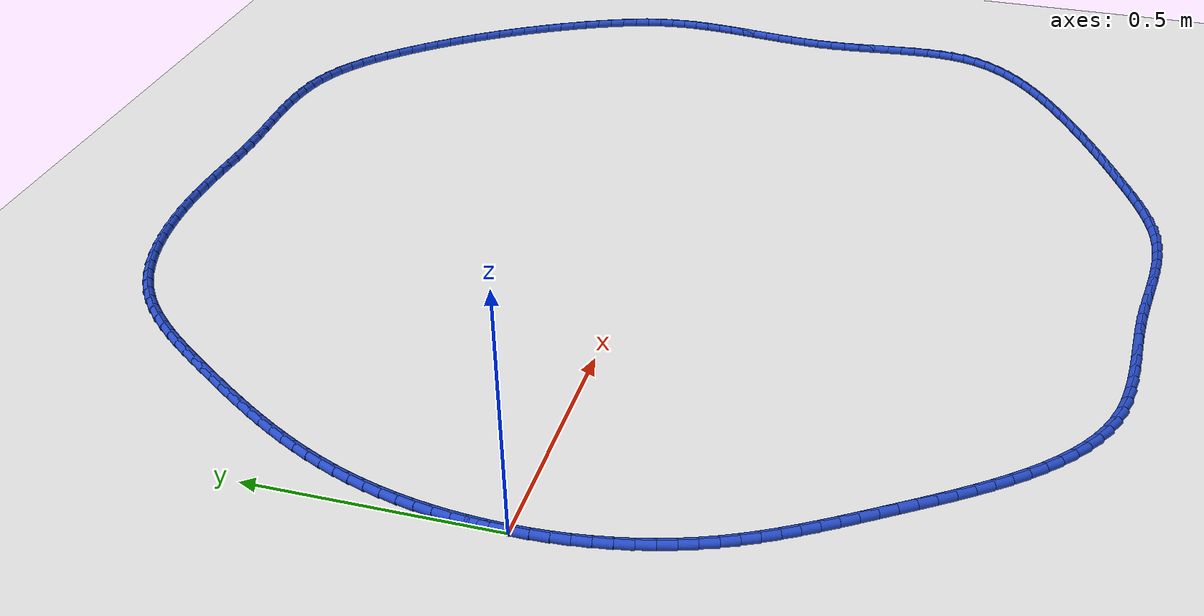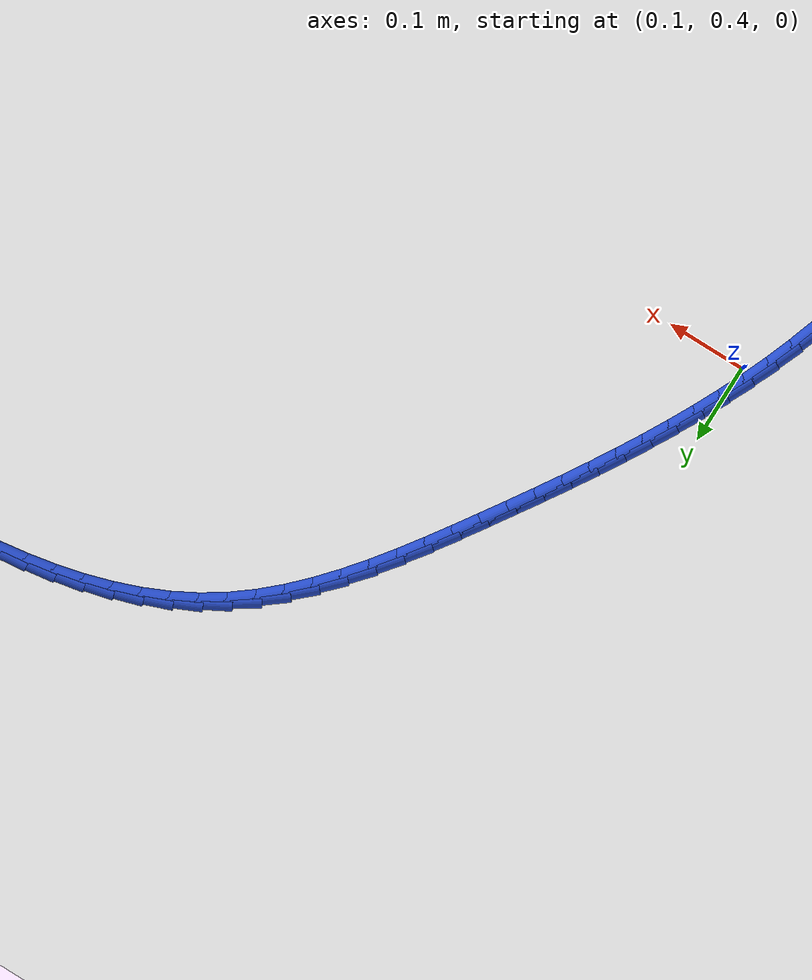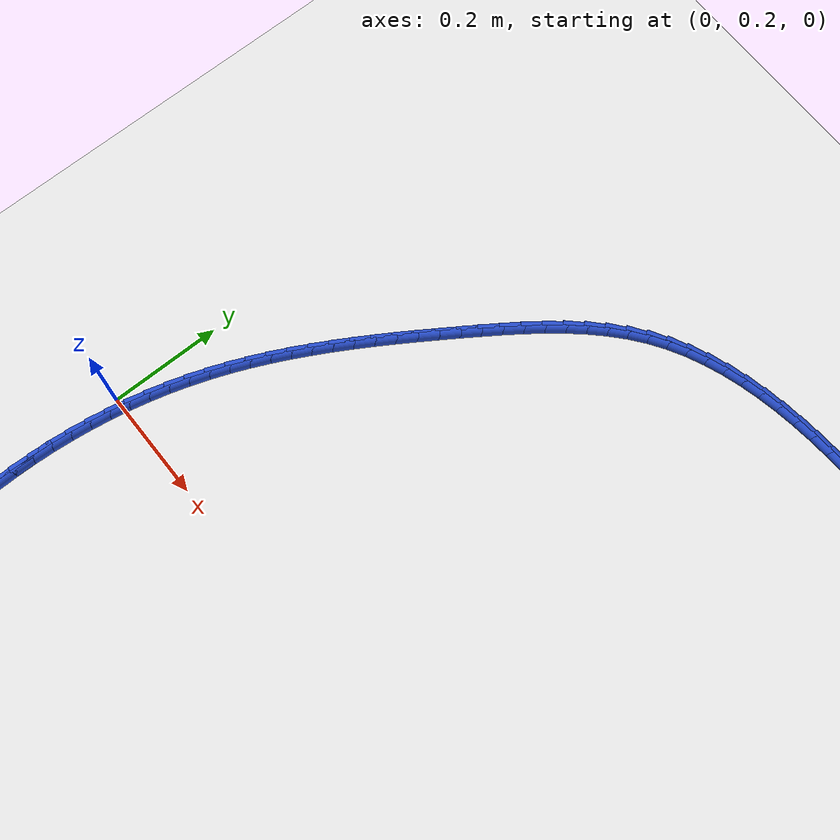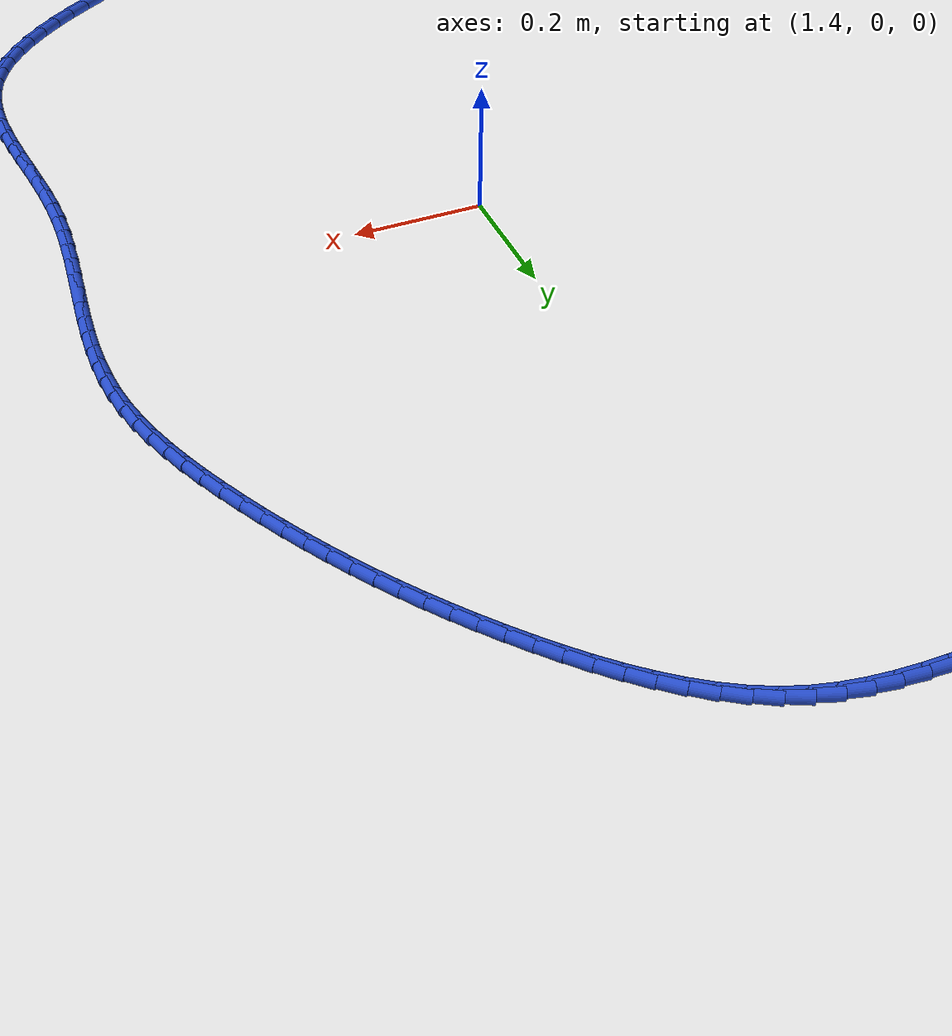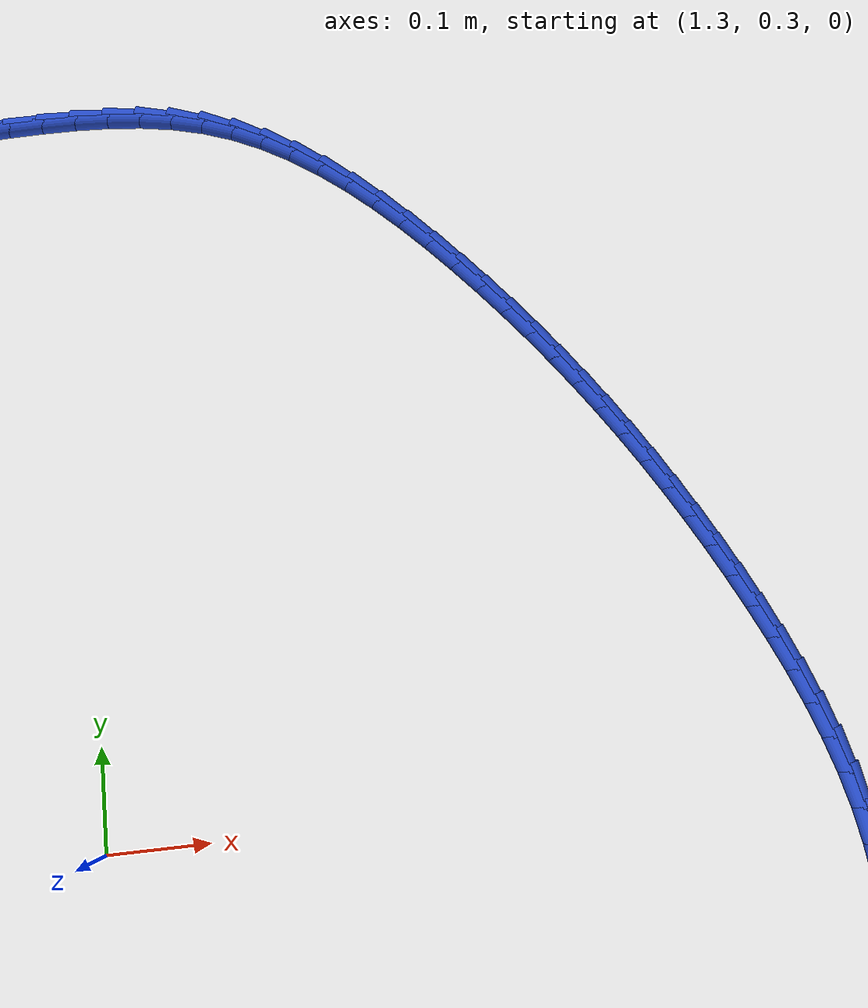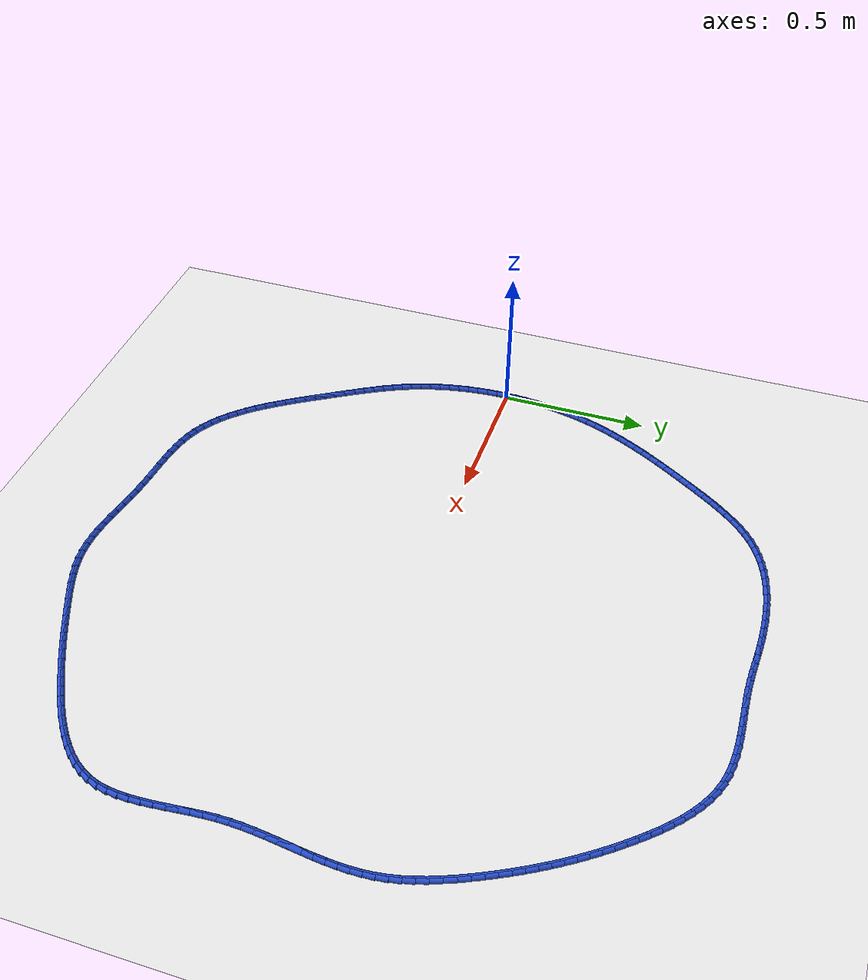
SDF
<sdf version="1.6">
 <world name="default">
  <light name="sun" type="directional">
   <pose>0 0 10 0 -0 0</pose>
   <diffuse>0.8 0.8 0.8 1</diffuse>
   <specular>0.2 0.2 0.2 1</specular>
   <attenuation>
    <range>1000</range>
    <constant>0.9</constant>
    <linear>0.01</linear>
    <quadratic>0.001</quadratic>
   </attenuation>
   <direction>-0.5 0.1 -0.9</direction>
  </light>
  <model name="ground_plane">
   <static>1</static>
   <link name="link">
    <collision name="collision">
     <geometry><plane><normal>0 0 1</normal><size>100 100</size></plane></geometry>
     <surface><friction><ode><mu>100</mu><mu2>50</mu2></ode></friction></surface>
    </collision>
    <visual name="visual">
     <cast_shadows>0</cast_shadows>
     <geometry><plane><normal>0 0 1</normal><size>100 100</size></plane></geometry>
     <material>
      <script><uri>file://media/materials/scripts/gazebo.material</uri><name>Gazebo/WhiteGlow</name></script>
     </material>
    </visual>
   </link>
  </model>
  <gravity>0 0 -9.8</gravity>
  <magnetic_field>6e-06 2.3e-05 -4.2e-05</magnetic_field>
  <atmosphere type="adiabatic"/>
  <physics name="default_physics" default="0" type="ode">
   <max_step_size>0.001</max_step_size>
   <real_time_factor>1</real_time_factor>
   <real_time_update_rate>1000</real_time_update_rate>
  </physics>
  <scene><ambient>0.4 0.4 0.4 1</ambient><background>0.7 0.7 0.7 1</background><shadows>1</shadows></scene>
  <spherical_coordinates>
   <surface_model>EARTH_WGS84</surface_model>
   <latitude_deg>0</latitude_deg>
   <longitude_deg>0</longitude_deg>
   <elevation>0</elevation>
   <heading_deg>0</heading_deg>
  </spherical_coordinates>
  <model name="line">
   <link name="link_0">
    <pose>1.734723475976807e-17 -4.163336342344337e-17 0.01 0 1.57 1.5488083871747154</pose>
    <collision name="collision">
     <geometry><cylinder><radius>0.01</radius><length>0.08</length></cylinder></geometry>
    </collision>
    <visual name="visual">
     <material>
      <script><name>Gazebo/Blue</name><uri>file://media/materials/scripts/gazebo.material</uri></script>
     </material>
     <geometry><cylinder><radius>0.01</radius><length>0.08</length></cylinder></geometry>
    </visual>
   </link>
   <link name="link_1">
    <pose>0.0007827353338297464 0.03559265671994102 0.01 0 1.57 1.5147372161107195</pose>
    <collision name="collision">
     <geometry><cylinder><radius>0.01</radius><length>0.08</length></cylinder></geometry>
    </collision>
    <visual name="visual">
     <material>
      <script><name>Gazebo/Blue</name><uri>file://media/materials/scripts/gazebo.material</uri></script>
     </material>
     <geometry><cylinder><radius>0.01</radius><length>0.08</length></cylinder></geometry>
    </visual>
   </link>
   <link name="link_2">
    <pose>0.002774547305765217 0.0710859958950458 0.01 0 1.57 1.4806242775169383</pose>
    <collision name="collision">
     <geometry><cylinder><radius>0.01</radius><length>0.08</length></cylinder></geometry>
    </collision>
    <visual name="visual">
     <material>
      <script><name>Gazebo/Blue</name><uri>file://media/materials/scripts/gazebo.material</uri></script>
     </material>
     <geometry><cylinder><radius>0.01</radius><length>0.08</length></cylinder></geometry>
    </visual>
   </link>
   <link name="link_3">
    <pose>0.005970378362178981 0.10643136751774934 0.01 0 1.57 1.4464077638140527</pose>
    <collision name="collision">
     <geometry><cylinder><radius>0.01</radius><length>0.08</length></cylinder></geometry>
    </collision>
    <visual name="visual">
     <material>
      <script><name>Gazebo/Blue</name><uri>file://media/materials/scripts/gazebo.material</uri></script>
     </material>
     <geometry><cylinder><radius>0.01</radius><length>0.08</length></cylinder></geometry>
    </visual>
   </link>
   <link name="link_4">
    <pose>0.0103651709494436 0.14158012158048672 0.01 0 1.57 1.41202545025935</pose>
    <collision name="collision">
     <geometry><cylinder><radius>0.01</radius><length>0.08</length></cylinder></geometry>
    </collision>
    <visual name="visual">
     <material>
      <script><name>Gazebo/Blue</name><uri>file://media/materials/scripts/gazebo.material</uri></script>
     </material>
     <geometry><cylinder><radius>0.01</radius><length>0.08</length></cylinder></geometry>
    </visual>
   </link>
   <link name="link_5">
    <pose>0.01595386751393163 0.17648360807569297 0.01 0 1.57 1.3774149393160502</pose>
    <collision name="collision">
     <geometry><cylinder><radius>0.01</radius><length>0.08</length></cylinder></geometry>
    </collision>
    <visual name="visual">
     <material>
      <script><name>Gazebo/Blue</name><uri>file://media/materials/scripts/gazebo.material</uri></script>
     </material>
     <geometry><cylinder><radius>0.01</radius><length>0.08</length></cylinder></geometry>
    </visual>
   </link>
   <link name="link_6">
    <pose>0.022731410502015617 0.21109317699580313 0.01 0 1.57 1.3425139329978768</pose>
    <collision name="collision">
     <geometry><cylinder><radius>0.01</radius><length>0.08</length></cylinder></geometry>
    </collision>
    <visual name="visual">
     <material>
      <script><name>Gazebo/Blue</name><uri>file://media/materials/scripts/gazebo.material</uri></script>
     </material>
     <geometry><cylinder><radius>0.01</radius><length>0.08</length></cylinder></geometry>
    </visual>
   </link>
   <link name="link_7">
    <pose>0.03069274236006813 0.2453601783332523 0.01 0 1.57 1.3072605463599958</pose>
    <collision name="collision">
     <geometry><cylinder><radius>0.01</radius><length>0.08</length></cylinder></geometry>
    </collision>
    <visual name="visual">
     <material>
      <script><name>Gazebo/Blue</name><uri>file://media/materials/scripts/gazebo.material</uri></script>
     </material>
     <geometry><cylinder><radius>0.01</radius><length>0.08</length></cylinder></geometry>
    </visual>
   </link>
   <link name="link_8">
    <pose>0.03983280553446171 0.2792359620804754 0.01 0 1.57 1.2715936756296164</pose>
    <collision name="collision">
     <geometry><cylinder><radius>0.01</radius><length>0.08</length></cylinder></geometry>
    </collision>
    <visual name="visual">
     <material>
      <script><name>Gazebo/Blue</name><uri>file://media/materials/scripts/gazebo.material</uri></script>
     </material>
     <geometry><cylinder><radius>0.01</radius><length>0.08</length></cylinder></geometry>
    </visual>
   </link>
   <link name="link_9">
    <pose>0.050146542471568925 0.3126718782299076 0.01 0 1.57 1.2355716873333757</pose>
    <collision name="collision">
     <geometry><cylinder><radius>0.01</radius><length>0.08</length></cylinder></geometry>
    </collision>
    <visual name="visual">
     <material>
      <script><name>Gazebo/Blue</name><uri>file://media/materials/scripts/gazebo.material</uri></script>
     </material>
     <geometry><cylinder><radius>0.01</radius><length>0.08</length></cylinder></geometry>
    </visual>
   </link>
   <link name="link_10">
    <pose>0.06162587702154166 0.3456231535175326 0.01 0 1.57 1.200718942186717</pose>
    <collision name="collision">
     <geometry><cylinder><radius>0.01</radius><length>0.08</length></cylinder></geometry>
    </collision>
    <visual name="visual">
     <material>
      <script><name>Gazebo/Blue</name><uri>file://media/materials/scripts/gazebo.material</uri></script>
     </material>
     <geometry><cylinder><radius>0.01</radius><length>0.08</length></cylinder></geometry>
    </visual>
   </link>
   <link name="link_11">
    <pose>0.07422353779214312 0.37809535261523775 0.01 0 1.57 1.1682134684397811</pose>
    <collision name="collision">
     <geometry><cylinder><radius>0.01</radius><length>0.08</length></cylinder></geometry>
    </collision>
    <visual name="visual">
     <material>
      <script><name>Gazebo/Blue</name><uri>file://media/materials/scripts/gazebo.material</uri></script>
     </material>
     <geometry><cylinder><radius>0.01</radius><length>0.08</length></cylinder></geometry>
    </visual>
   </link>
   <link name="link_12">
    <pose>0.0878648702748198 0.4101292079721699 0.01 0 1.57 1.1381771511669305</pose>
    <collision name="collision">
     <geometry><cylinder><radius>0.01</radius><length>0.08</length></cylinder></geometry>
    </collision>
    <visual name="visual">
     <material>
      <script><name>Gazebo/Blue</name><uri>file://media/materials/scripts/gazebo.material</uri></script>
     </material>
     <geometry><cylinder><radius>0.01</radius><length>0.08</length></cylinder></geometry>
    </visual>
   </link>
   <link name="link_13">
    <pose>0.1024746594522828 0.44176617189149636 0.01 0 1.57 1.1106772916666237</pose>
    <collision name="collision">
     <geometry><cylinder><radius>0.01</radius><length>0.08</length></cylinder></geometry>
    </collision>
    <visual name="visual">
     <material>
      <script><name>Gazebo/Blue</name><uri>file://media/materials/scripts/gazebo.material</uri></script>
     </material>
     <geometry><cylinder><radius>0.01</radius><length>0.08</length></cylinder></geometry>
    </visual>
   </link>
   <link name="link_14">
    <pose>0.11797769030724309 0.47304769667638397 0.01 0 1.57 1.085753314319258</pose>
    <collision name="collision">
     <geometry><cylinder><radius>0.01</radius><length>0.08</length></cylinder></geometry>
    </collision>
    <visual name="visual">
     <material>
      <script><name>Gazebo/Blue</name><uri>file://media/materials/scripts/gazebo.material</uri></script>
     </material>
     <geometry><cylinder><radius>0.01</radius><length>0.08</length></cylinder></geometry>
    </visual>
   </link>
   <link name="link_15">
    <pose>0.13429874782241183 0.5040152346300001 0.01 0 1.57 1.063421792630666</pose>
    <collision name="collision">
     <geometry><cylinder><radius>0.01</radius><length>0.08</length></cylinder></geometry>
    </collision>
    <visual name="visual">
     <material>
      <script><name>Gazebo/Blue</name><uri>file://media/materials/scripts/gazebo.material</uri></script>
     </material>
     <geometry><cylinder><radius>0.01</radius><length>0.08</length></cylinder></geometry>
    </visual>
   </link>
   <link name="link_16">
    <pose>0.15136261698050008 0.5347102380555118 0.01 0 1.57 1.0436813862849401</pose>
    <collision name="collision">
     <geometry><cylinder><radius>0.01</radius><length>0.08</length></cylinder></geometry>
    </collision>
    <visual name="visual">
     <material>
      <script><name>Gazebo/Blue</name><uri>file://media/materials/scripts/gazebo.material</uri></script>
     </material>
     <geometry><cylinder><radius>0.01</radius><length>0.08</length></cylinder></geometry>
    </visual>
   </link>
   <link name="link_17">
    <pose>0.16909408276421878 0.5651741592560859 0.01 0 1.57 1.0265174313644143</pose>
    <collision name="collision">
     <geometry><cylinder><radius>0.01</radius><length>0.08</length></cylinder></geometry>
    </collision>
    <visual name="visual">
     <material>
      <script><name>Gazebo/Blue</name><uri>file://media/materials/scripts/gazebo.material</uri></script>
     </material>
     <geometry><cylinder><radius>0.01</radius><length>0.08</length></cylinder></geometry>
    </visual>
   </link>
   <link name="link_18">
    <pose>0.18741793015627908 0.59544845053489 0.01 0 1.57 1.0119060225093495</pose>
    <collision name="collision">
     <geometry><cylinder><radius>0.01</radius><length>0.08</length></cylinder></geometry>
    </collision>
    <visual name="visual">
     <material>
      <script><name>Gazebo/Blue</name><uri>file://media/materials/scripts/gazebo.material</uri></script>
     </material>
     <geometry><cylinder><radius>0.01</radius><length>0.08</length></cylinder></geometry>
    </visual>
   </link>
   <link name="link_19">
    <pose>0.206258944139392 0.625574564195091 0.01 0 1.57 0.9998175044152179</pose>
    <collision name="collision">
     <geometry><cylinder><radius>0.01</radius><length>0.08</length></cylinder></geometry>
    </collision>
    <visual name="visual">
     <material>
      <script><name>Gazebo/Blue</name><uri>file://media/materials/scripts/gazebo.material</uri></script>
     </material>
     <geometry><cylinder><radius>0.01</radius><length>0.08</length></cylinder></geometry>
    </visual>
   </link>
   <link name="link_20">
    <pose>0.22554190969626864 0.6555939525398561 0.01 0 1.57 0.9902193480513775</pose>
    <collision name="collision">
     <geometry><cylinder><radius>0.01</radius><length>0.08</length></cylinder></geometry>
    </collision>
    <visual name="visual">
     <material>
      <script><name>Gazebo/Blue</name><uri>file://media/materials/scripts/gazebo.material</uri></script>
     </material>
     <geometry><cylinder><radius>0.01</radius><length>0.08</length></cylinder></geometry>
    </visual>
   </link>
   <link name="link_21">
    <pose>0.24519161180962 0.6855480678723522 0.01 0 1.57 0.9830784254898436</pose>
    <collision name="collision">
     <geometry><cylinder><radius>0.01</radius><length>0.08</length></cylinder></geometry>
    </collision>
    <visual name="visual">
     <material>
      <script><name>Gazebo/Blue</name><uri>file://media/materials/scripts/gazebo.material</uri></script>
     </material>
     <geometry><cylinder><radius>0.01</radius><length>0.08</length></cylinder></geometry>
    </visual>
   </link>
   <link name="link_22">
    <pose>0.26513283546215727 0.7154783624957468 0.01 0 1.57 0.9776945148816585</pose>
    <collision name="collision">
     <geometry><cylinder><radius>0.01</radius><length>0.08</length></cylinder></geometry>
    </collision>
    <visual name="visual">
     <material>
      <script><name>Gazebo/Blue</name><uri>file://media/materials/scripts/gazebo.material</uri></script>
     </material>
     <geometry><cylinder><radius>0.01</radius><length>0.08</length></cylinder></geometry>
    </visual>
   </link>
   <link name="link_23">
    <pose>0.2853058584788981 0.7454061159215244 0.01 0 1.57 0.967878978523106</pose>
    <collision name="collision">
     <geometry><cylinder><radius>0.01</radius><length>0.08</length></cylinder></geometry>
    </collision>
    <visual name="visual">
     <material>
      <script><name>Gazebo/Blue</name><uri>file://media/materials/scripts/gazebo.material</uri></script>
     </material>
     <geometry><cylinder><radius>0.01</radius><length>0.08</length></cylinder></geometry>
    </visual>
   </link>
   <link name="link_24">
    <pose>0.3057938141007421 0.7751665996654674 0.01 0 1.57 0.9502201856580623</pose>
    <collision name="collision">
     <geometry><cylinder><radius>0.01</radius><length>0.08</length></cylinder></geometry>
    </collision>
    <visual name="visual">
     <material>
      <script><name>Gazebo/Blue</name><uri>file://media/materials/scripts/gazebo.material</uri></script>
     </material>
     <geometry><cylinder><radius>0.01</radius><length>0.08</length></cylinder></geometry>
    </visual>
   </link>
   <link name="link_25">
    <pose>0.3267569302952169 0.8044947023807894 0.01 0 1.57 0.9244615560032429</pose>
    <collision name="collision">
     <geometry><cylinder><radius>0.01</radius><length>0.08</length></cylinder></geometry>
    </collision>
    <visual name="visual">
     <material>
      <script><name>Gazebo/Blue</name><uri>file://media/materials/scripts/gazebo.material</uri></script>
     </material>
     <geometry><cylinder><radius>0.01</radius><length>0.08</length></cylinder></geometry>
    </visual>
   </link>
   <link name="link_26">
    <pose>0.3483561857329221 0.8331243352514734 0.01 0 1.57 0.8902568233275683</pose>
    <collision name="collision">
     <geometry><cylinder><radius>0.01</radius><length>0.08</length></cylinder></geometry>
    </collision>
    <visual name="visual">
     <material>
      <script><name>Gazebo/Blue</name><uri>file://media/materials/scripts/gazebo.material</uri></script>
     </material>
     <geometry><cylinder><radius>0.01</radius><length>0.08</length></cylinder></geometry>
    </visual>
   </link>
   <link name="link_27">
    <pose>0.37075255908445615 0.8607894094615016 0.01 0 1.57 0.8471797514674192</pose>
    <collision name="collision">
     <geometry><cylinder><radius>0.01</radius><length>0.08</length></cylinder></geometry>
    </collision>
    <visual name="visual">
     <material>
      <script><name>Gazebo/Blue</name><uri>file://media/materials/scripts/gazebo.material</uri></script>
     </material>
     <geometry><cylinder><radius>0.01</radius><length>0.08</length></cylinder></geometry>
    </visual>
   </link>
   <link name="link_28">
    <pose>0.3941070290204181 0.8872238361948566 0.01 0 1.57 0.7947914034711339</pose>
    <collision name="collision">
     <geometry><cylinder><radius>0.01</radius><length>0.08</length></cylinder></geometry>
    </collision>
    <visual name="visual">
     <material>
      <script><name>Gazebo/Blue</name><uri>file://media/materials/scripts/gazebo.material</uri></script>
     </material>
     <geometry><cylinder><radius>0.01</radius><length>0.08</length></cylinder></geometry>
    </visual>
   </link>
   <link name="link_29">
    <pose>0.41858057421140715 0.9121615266355211 0.01 0 1.57 0.7327427181305164</pose>
    <collision name="collision">
     <geometry><cylinder><radius>0.01</radius><length>0.08</length></cylinder></geometry>
    </collision>
    <visual name="visual">
     <material>
      <script><name>Gazebo/Blue</name><uri>file://media/materials/scripts/gazebo.material</uri></script>
     </material>
     <geometry><cylinder><radius>0.01</radius><length>0.08</length></cylinder></geometry>
    </visual>
   </link>
   <link name="link_30">
    <pose>0.444334173328022 0.9353363919674778 0.01 0 1.57 0.660918773126957</pose>
    <collision name="collision">
     <geometry><cylinder><radius>0.01</radius><length>0.08</length></cylinder></geometry>
    </collision>
    <visual name="visual">
     <material>
      <script><name>Gazebo/Blue</name><uri>file://media/materials/scripts/gazebo.material</uri></script>
     </material>
     <geometry><cylinder><radius>0.01</radius><length>0.08</length></cylinder></geometry>
    </visual>
   </link>
   <link name="link_31">
    <pose>0.4715288050408617 0.9564823433747088 0.01 0 1.57 0.5801661426976136</pose>
    <collision name="collision">
     <geometry><cylinder><radius>0.01</radius><length>0.08</length></cylinder></geometry>
    </collision>
    <visual name="visual">
     <material>
      <script><name>Gazebo/Blue</name><uri>file://media/materials/scripts/gazebo.material</uri></script>
     </material>
     <geometry><cylinder><radius>0.01</radius><length>0.08</length></cylinder></geometry>
    </visual>
   </link>
   <link name="link_32">
    <pose>0.5003129685951782 0.9753476549547179 0.01 0 1.57 0.49927126204519856</pose>
    <collision name="collision">
     <geometry><cylinder><radius>0.01</radius><length>0.08</length></cylinder></geometry>
    </collision>
    <visual name="visual">
     <material>
      <script><name>Gazebo/Blue</name><uri>file://media/materials/scripts/gazebo.material</uri></script>
     </material>
     <geometry><cylinder><radius>0.01</radius><length>0.08</length></cylinder></geometry>
    </visual>
   </link>
   <link name="link_33">
    <pose>0.5306509160144802 0.9918926559949465 0.01 0 1.57 0.4248155415951112</pose>
    <collision name="collision">
     <geometry><cylinder><radius>0.01</radius><length>0.08</length></cylinder></geometry>
    </collision>
    <visual name="visual">
     <material>
      <script><name>Gazebo/Blue</name><uri>file://media/materials/scripts/gazebo.material</uri></script>
     </material>
     <geometry><cylinder><radius>0.01</radius><length>0.08</length></cylinder></geometry>
    </visual>
   </link>
   <link name="link_34">
    <pose>0.5623663242166497 1.0062394675343898 0.01 0 1.57 0.3569700147139003</pose>
    <collision name="collision">
     <geometry><cylinder><radius>0.01</radius><length>0.08</length></cylinder></geometry>
    </collision>
    <visual name="visual">
     <material>
      <script><name>Gazebo/Blue</name><uri>file://media/materials/scripts/gazebo.material</uri></script>
     </material>
     <geometry><cylinder><radius>0.01</radius><length>0.08</length></cylinder></geometry>
    </visual>
   </link>
   <link name="link_35">
    <pose>0.5952793260055935 1.0185142896301944 0.01 0 1.57 0.2955025873966272</pose>
    <collision name="collision">
     <geometry><cylinder><radius>0.01</radius><length>0.08</length></cylinder></geometry>
    </collision>
    <visual name="visual">
     <material>
      <script><name>Gazebo/Blue</name><uri>file://media/materials/scripts/gazebo.material</uri></script>
     </material>
     <geometry><cylinder><radius>0.01</radius><length>0.08</length></cylinder></geometry>
    </visual>
   </link>
   <link name="link_36">
    <pose>0.6292100541852201 1.0288433223395073 0.01 0 1.57 0.24002684648910314</pose>
    <collision name="collision">
     <geometry><cylinder><radius>0.01</radius><length>0.08</length></cylinder></geometry>
    </collision>
    <visual name="visual">
     <material>
      <script><name>Gazebo/Blue</name><uri>file://media/materials/scripts/gazebo.material</uri></script>
     </material>
     <geometry><cylinder><radius>0.01</radius><length>0.08</length></cylinder></geometry>
    </visual>
   </link>
   <link name="link_37">
    <pose>0.6639786415594363 1.037352765719475 0.01 0 1.57 0.19007676412731167</pose>
    <collision name="collision">
     <geometry><cylinder><radius>0.01</radius><length>0.08</length></cylinder></geometry>
    </collision>
    <visual name="visual">
     <material>
      <script><name>Gazebo/Blue</name><uri>file://media/materials/scripts/gazebo.material</uri></script>
     </material>
     <geometry><cylinder><radius>0.01</radius><length>0.08</length></cylinder></geometry>
    </visual>
   </link>
   <link name="link_38">
    <pose>0.6994052209321502 1.0441688198272443 0.01 0 1.57 0.14516052504687696</pose>
    <collision name="collision">
     <geometry><cylinder><radius>0.01</radius><length>0.08</length></cylinder></geometry>
    </collision>
    <visual name="visual">
     <material>
      <script><name>Gazebo/Blue</name><uri>file://media/materials/scripts/gazebo.material</uri></script>
     </material>
     <geometry><cylinder><radius>0.01</radius><length>0.08</length></cylinder></geometry>
    </visual>
   </link>
   <link name="link_39">
    <pose>0.735309925107269 1.049417684719962 0.01 0 1.57 0.10479600865793186</pose>
    <collision name="collision">
     <geometry><cylinder><radius>0.01</radius><length>0.08</length></cylinder></geometry>
    </collision>
    <visual name="visual">
     <material>
      <script><name>Gazebo/Blue</name><uri>file://media/materials/scripts/gazebo.material</uri></script>
     </material>
     <geometry><cylinder><radius>0.01</radius><length>0.08</length></cylinder></geometry>
    </visual>
   </link>
   <link name="link_40">
    <pose>0.7715128868887005 1.0532255604547751 0.01 0 1.57 0.06853220484784232</pose>
    <collision name="collision">
     <geometry><cylinder><radius>0.01</radius><length>0.08</length></cylinder></geometry>
    </collision>
    <visual name="visual">
     <material>
      <script><name>Gazebo/Blue</name><uri>file://media/materials/scripts/gazebo.material</uri></script>
     </material>
     <geometry><cylinder><radius>0.01</radius><length>0.08</length></cylinder></geometry>
    </visual>
   </link>
   <link name="link_41">
    <pose>0.8078342390803522 1.0557186470888298 0.01 0 1.57 0.03596083025836046</pose>
    <collision name="collision">
     <geometry><cylinder><radius>0.01</radius><length>0.08</length></cylinder></geometry>
    </collision>
    <visual name="visual">
     <material>
      <script><name>Gazebo/Blue</name><uri>file://media/materials/scripts/gazebo.material</uri></script>
     </material>
     <geometry><cylinder><radius>0.01</radius><length>0.08</length></cylinder></geometry>
    </visual>
   </link>
   <link name="link_42">
    <pose>0.8440941144861316 1.057023144679273 0.01 0 1.57 0.006721677652159711</pose>
    <collision name="collision">
     <geometry><cylinder><radius>0.01</radius><length>0.08</length></cylinder></geometry>
    </collision>
    <visual name="visual">
     <material>
      <script><name>Gazebo/Blue</name><uri>file://media/materials/scripts/gazebo.material</uri></script>
     </material>
     <geometry><cylinder><radius>0.01</radius><length>0.08</length></cylinder></geometry>
    </visual>
   </link>
   <link name="link_43">
    <pose>0.8801126459099462 1.0572652532832514 0.01 0 1.57 -0.01923687257203054</pose>
    <collision name="collision">
     <geometry><cylinder><radius>0.01</radius><length>0.08</length></cylinder></geometry>
    </collision>
    <visual name="visual">
     <material>
      <script><name>Gazebo/Blue</name><uri>file://media/materials/scripts/gazebo.material</uri></script>
     </material>
     <geometry><cylinder><radius>0.01</radius><length>0.08</length></cylinder></geometry>
    </visual>
   </link>
   <link name="link_44">
    <pose>0.9157230908402902 1.0565801351788304 0.01 0 1.57 -0.038300130499265984</pose>
    <collision name="collision">
     <geometry><cylinder><radius>0.01</radius><length>0.08</length></cylinder></geometry>
    </collision>
    <visual name="visual">
     <material>
      <script><name>Gazebo/Blue</name><uri>file://media/materials/scripts/gazebo.material</uri></script>
     </material>
     <geometry><cylinder><radius>0.01</radius><length>0.08</length></cylinder></geometry>
    </visual>
   </link>
   <link name="link_45">
    <pose>0.9509454271535249 1.0552304550884237 0.01 0 1.57 -0.047308073980665534</pose>
    <collision name="collision">
     <geometry><cylinder><radius>0.01</radius><length>0.08</length></cylinder></geometry>
    </collision>
    <visual name="visual">
     <material>
      <script><name>Gazebo/Blue</name><uri>file://media/materials/scripts/gazebo.material</uri></script>
     </material>
     <geometry><cylinder><radius>0.01</radius><length>0.08</length></cylinder></geometry>
    </visual>
   </link>
   <link name="link_46">
    <pose>0.9859385829001164 1.0535737601789557 0.01 0 1.57 -0.04589038742514017</pose>
    <collision name="collision">
     <geometry><cylinder><radius>0.01</radius><length>0.08</length></cylinder></geometry>
    </collision>
    <visual name="visual">
     <material>
      <script><name>Gazebo/Blue</name><uri>file://media/materials/scripts/gazebo.material</uri></script>
     </material>
     <geometry><cylinder><radius>0.01</radius><length>0.08</length></cylinder></geometry>
    </visual>
   </link>
   <link name="link_47">
    <pose>1.0208647944899616 1.0519698567381635 0.01 0 1.57 -0.03400329453485656</pose>
    <collision name="collision">
     <geometry><cylinder><radius>0.01</radius><length>0.08</length></cylinder></geometry>
    </collision>
    <visual name="visual">
     <material>
      <script><name>Gazebo/Blue</name><uri>file://media/materials/scripts/gazebo.material</uri></script>
     </material>
     <geometry><cylinder><radius>0.01</radius><length>0.08</length></cylinder></geometry>
    </visual>
   </link>
   <link name="link_48">
    <pose>1.0558862983329584 1.0507785510537846 0.01 0 1.57 -0.011873396888905794</pose>
    <collision name="collision">
     <geometry><cylinder><radius>0.01</radius><length>0.08</length></cylinder></geometry>
    </collision>
    <visual name="visual">
     <material>
      <script><name>Gazebo/Blue</name><uri>file://media/materials/scripts/gazebo.material</uri></script>
     </material>
     <geometry><cylinder><radius>0.01</radius><length>0.08</length></cylinder></geometry>
    </visual>
   </link>
   <link name="link_49">
    <pose>1.0911653308390044 1.0503596494135559 0.01 0 1.57 0.01660576008801761</pose>
    <collision name="collision">
     <geometry><cylinder><radius>0.01</radius><length>0.08</length></cylinder></geometry>
    </collision>
    <visual name="visual">
     <material>
      <script><name>Gazebo/Blue</name><uri>file://media/materials/scripts/gazebo.material</uri></script>
     </material>
     <geometry><cylinder><radius>0.01</radius><length>0.08</length></cylinder></geometry>
    </visual>
   </link>
   <link name="link_50">
    <pose>1.1268173604423681 1.0509517328873903 0.01 0 1.57 0.036641509146488796</pose>
    <collision name="collision">
     <geometry><cylinder><radius>0.01</radius><length>0.08</length></cylinder></geometry>
    </collision>
    <visual name="visual">
     <material>
      <script><name>Gazebo/Blue</name><uri>file://media/materials/scripts/gazebo.material</uri></script>
     </material>
     <geometry><cylinder><radius>0.01</radius><length>0.08</length></cylinder></geometry>
    </visual>
   </link>
   <link name="link_51">
    <pose>1.1627556113981965 1.0522691542813485 0.01 0 1.57 0.04474015202123307</pose>
    <collision name="collision">
     <geometry><cylinder><radius>0.01</radius><length>0.08</length></cylinder></geometry>
    </collision>
    <visual name="visual">
     <material>
      <script><name>Gazebo/Blue</name><uri>file://media/materials/scripts/gazebo.material</uri></script>
     </material>
     <geometry><cylinder><radius>0.01</radius><length>0.08</length></cylinder></geometry>
    </visual>
   </link>
   <link name="link_52">
    <pose>1.1988386511875166 1.053884592975197 0.01 0 1.57 0.041159382962036015</pose>
    <collision name="collision">
     <geometry><cylinder><radius>0.01</radius><length>0.08</length></cylinder></geometry>
    </collision>
    <visual name="visual">
     <material>
      <script><name>Gazebo/Blue</name><uri>file://media/materials/scripts/gazebo.material</uri></script>
     </material>
     <geometry><cylinder><radius>0.01</radius><length>0.08</length></cylinder></geometry>
    </visual>
   </link>
   <link name="link_53">
    <pose>1.234925046403441 1.0553707260471774 0.01 0 1.57 0.02585093092150613</pose>
    <collision name="collision">
     <geometry><cylinder><radius>0.01</radius><length>0.08</length></cylinder></geometry>
    </collision>
    <visual name="visual">
     <material>
      <script><name>Gazebo/Blue</name><uri>file://media/materials/scripts/gazebo.material</uri></script>
     </material>
     <geometry><cylinder><radius>0.01</radius><length>0.08</length></cylinder></geometry>
    </visual>
   </link>
   <link name="link_54">
    <pose>1.2708733636390825 1.056300230575531 0.01 0 1.57 -0.0015264568983469004</pose>
    <collision name="collision">
     <geometry><cylinder><radius>0.01</radius><length>0.08</length></cylinder></geometry>
    </collision>
    <visual name="visual">
     <material>
      <script><name>Gazebo/Blue</name><uri>file://media/materials/scripts/gazebo.material</uri></script>
     </material>
     <geometry><cylinder><radius>0.01</radius><length>0.08</length></cylinder></geometry>
    </visual>
   </link>
   <link name="link_55">
    <pose>1.3065421694875534 1.0562457836384993 0.01 0 1.57 -0.04155932670738052</pose>
    <collision name="collision">
     <geometry><cylinder><radius>0.01</radius><length>0.08</length></cylinder></geometry>
    </collision>
    <visual name="visual">
     <material>
      <script><name>Gazebo/Blue</name><uri>file://media/materials/scripts/gazebo.material</uri></script>
     </material>
     <geometry><cylinder><radius>0.01</radius><length>0.08</length></cylinder></geometry>
    </visual>
   </link>
   <link name="link_56">
    <pose>1.3417900305419659 1.0547800623143235 0.01 0 1.57 -0.09497854373912477</pose>
    <collision name="collision">
     <geometry><cylinder><radius>0.01</radius><length>0.08</length></cylinder></geometry>
    </collision>
    <visual name="visual">
     <material>
      <script><name>Gazebo/Blue</name><uri>file://media/materials/scripts/gazebo.material</uri></script>
     </material>
     <geometry><cylinder><radius>0.01</radius><length>0.08</length></cylinder></geometry>
    </visual>
   </link>
   <link name="link_57">
    <pose>1.3764755133954334 1.0514757436812454 0.01 0 1.57 -0.16247400914917456</pose>
    <collision name="collision">
     <geometry><cylinder><radius>0.01</radius><length>0.08</length></cylinder></geometry>
    </collision>
    <visual name="visual">
     <material>
      <script><name>Gazebo/Blue</name><uri>file://media/materials/scripts/gazebo.material</uri></script>
     </material>
     <geometry><cylinder><radius>0.01</radius><length>0.08</length></cylinder></geometry>
    </visual>
   </link>
   <link name="link_58">
    <pose>1.4104571846410678 1.0459055048175063 0.01 0 1.57 -0.24439277694548167</pose>
    <collision name="collision">
     <geometry><cylinder><radius>0.01</radius><length>0.08</length></cylinder></geometry>
    </collision>
    <visual name="visual">
     <material>
      <script><name>Gazebo/Blue</name><uri>file://media/materials/scripts/gazebo.material</uri></script>
     </material>
     <geometry><cylinder><radius>0.01</radius><length>0.08</length></cylinder></geometry>
    </visual>
   </link>
   <link name="link_59">
    <pose>1.4435936108719818 1.0376420228013477 0.01 0 1.57 -0.33973283939593607</pose>
    <collision name="collision">
     <geometry><cylinder><radius>0.01</radius><length>0.08</length></cylinder></geometry>
    </collision>
    <visual name="visual">
     <material>
      <script><name>Gazebo/Blue</name><uri>file://media/materials/scripts/gazebo.material</uri></script>
     </material>
     <geometry><cylinder><radius>0.01</radius><length>0.08</length></cylinder></geometry>
    </visual>
   </link>
   <link name="link_60">
    <pose>1.475747580032831 1.0262776423936242 0.01 0 1.57 -0.4357259390207915</pose>
    <collision name="collision">
     <geometry><cylinder><radius>0.01</radius><length>0.08</length></cylinder></geometry>
    </collision>
    <visual name="visual">
     <material>
      <script><name>Gazebo/Blue</name><uri>file://media/materials/scripts/gazebo.material</uri></script>
     </material>
     <geometry><cylinder><radius>0.01</radius><length>0.08</length></cylinder></geometry>
    </visual>
   </link>
   <link name="link_61">
    <pose>1.5068646769039717 1.01179046677153 0.01 0 1.57 -0.5211237562498636</pose>
    <collision name="collision">
     <geometry><cylinder><radius>0.01</radius><length>0.08</length></cylinder></geometry>
    </collision>
    <visual name="visual">
     <material>
      <script><name>Gazebo/Blue</name><uri>file://media/materials/scripts/gazebo.material</uri></script>
     </material>
     <geometry><cylinder><radius>0.01</radius><length>0.08</length></cylinder></geometry>
    </visual>
   </link>
   <link name="link_62">
    <pose>1.536966043668255 0.9945106283134046 0.01 0 1.57 -0.5956475045686934</pose>
    <collision name="collision">
     <geometry><cylinder><radius>0.01</radius><length>0.08</length></cylinder></geometry>
    </collision>
    <visual name="visual">
     <material>
      <script><name>Gazebo/Blue</name><uri>file://media/materials/scripts/gazebo.material</uri></script>
     </material>
     <geometry><cylinder><radius>0.01</radius><length>0.08</length></cylinder></geometry>
    </visual>
   </link>
   <link name="link_63">
    <pose>1.5660755921725842 0.9747811635286325 0.01 0 1.57 -0.6598932752715758</pose>
    <collision name="collision">
     <geometry><cylinder><radius>0.01</radius><length>0.08</length></cylinder></geometry>
    </collision>
    <visual name="visual">
     <material>
      <script><name>Gazebo/Blue</name><uri>file://media/materials/scripts/gazebo.material</uri></script>
     </material>
     <geometry><cylinder><radius>0.01</radius><length>0.08</length></cylinder></geometry>
    </visual>
   </link>
   <link name="link_64">
    <pose>1.5942172342638603 0.9529451089265967 0.01 0 1.57 -0.7146848854726908</pose>
    <collision name="collision">
     <geometry><cylinder><radius>0.01</radius><length>0.08</length></cylinder></geometry>
    </collision>
    <visual name="visual">
     <material>
      <script><name>Gazebo/Blue</name><uri>file://media/materials/scripts/gazebo.material</uri></script>
     </material>
     <geometry><cylinder><radius>0.01</radius><length>0.08</length></cylinder></geometry>
    </visual>
   </link>
   <link name="link_65">
    <pose>1.6214148817889869 0.9293455010166821 0.01 0 1.57 -0.7608904643502499</pose>
    <collision name="collision">
     <geometry><cylinder><radius>0.01</radius><length>0.08</length></cylinder></geometry>
    </collision>
    <visual name="visual">
     <material>
      <script><name>Gazebo/Blue</name><uri>file://media/materials/scripts/gazebo.material</uri></script>
     </material>
     <geometry><cylinder><radius>0.01</radius><length>0.08</length></cylinder></geometry>
    </visual>
   </link>
   <link name="link_66">
    <pose>1.6476924465948652 0.9043253763082731 0.01 0 1.57 -0.7993099502157914</pose>
    <collision name="collision">
     <geometry><cylinder><radius>0.01</radius><length>0.08</length></cylinder></geometry>
    </collision>
    <visual name="visual">
     <material>
      <script><name>Gazebo/Blue</name><uri>file://media/materials/scripts/gazebo.material</uri></script>
     </material>
     <geometry><cylinder><radius>0.01</radius><length>0.08</length></cylinder></geometry>
    </visual>
   </link>
   <link name="link_67">
    <pose>1.673073840528398 0.8782277713107528 0.01 0 1.57 -0.8306119778116339</pose>
    <collision name="collision">
     <geometry><cylinder><radius>0.01</radius><length>0.08</length></cylinder></geometry>
    </collision>
    <visual name="visual">
     <material>
      <script><name>Gazebo/Blue</name><uri>file://media/materials/scripts/gazebo.material</uri></script>
     </material>
     <geometry><cylinder><radius>0.01</radius><length>0.08</length></cylinder></geometry>
    </visual>
   </link>
   <link name="link_68">
    <pose>1.6975829754364877 0.851395722533506 0.01 0 1.57 -0.8556168227659977</pose>
    <collision name="collision">
     <geometry><cylinder><radius>0.01</radius><length>0.08</length></cylinder></geometry>
    </collision>
    <visual name="visual">
     <material>
      <script><name>Gazebo/Blue</name><uri>file://media/materials/scripts/gazebo.material</uri></script>
     </material>
     <geometry><cylinder><radius>0.01</radius><length>0.08</length></cylinder></geometry>
    </visual>
   </link>
   <link name="link_69">
    <pose>1.7212439045062655 0.8241546360581018 0.01 0 1.57 -0.8783148447744218</pose>
    <collision name="collision">
     <geometry><cylinder><radius>0.01</radius><length>0.08</length></cylinder></geometry>
    </collision>
    <visual name="visual">
     <material>
      <script><name>Gazebo/Blue</name><uri>file://media/materials/scripts/gazebo.material</uri></script>
     </material>
     <geometry><cylinder><radius>0.01</radius><length>0.08</length></cylinder></geometry>
    </visual>
   </link>
   <link name="link_70">
    <pose>1.7440823445247164 0.7966224046680949 0.01 0 1.57 -0.9011069313705637</pose>
    <collision name="collision">
     <geometry><cylinder><radius>0.01</radius><length>0.08</length></cylinder></geometry>
    </collision>
    <visual name="visual">
     <material>
      <script><name>Gazebo/Blue</name><uri>file://media/materials/scripts/gazebo.material</uri></script>
     </material>
     <geometry><cylinder><radius>0.01</radius><length>0.08</length></cylinder></geometry>
    </visual>
   </link>
   <link name="link_71">
    <pose>1.766125095393632 0.7687818161067946 0.01 0 1.57 -0.9239516656726985</pose>
    <collision name="collision">
     <geometry><cylinder><radius>0.01</radius><length>0.08</length></cylinder></geometry>
    </collision>
    <visual name="visual">
     <material>
      <script><name>Gazebo/Blue</name><uri>file://media/materials/scripts/gazebo.material</uri></script>
     </material>
     <geometry><cylinder><radius>0.01</radius><length>0.08</length></cylinder></geometry>
    </visual>
   </link>
   <link name="link_72">
    <pose>1.7873989755132862 0.7406133506626811 0.01 0 1.57 -0.9467638716363038</pose>
    <collision name="collision">
     <geometry><cylinder><radius>0.01</radius><length>0.08</length></cylinder></geometry>
    </collision>
    <visual name="visual">
     <material>
      <script><name>Gazebo/Blue</name><uri>file://media/materials/scripts/gazebo.material</uri></script>
     </material>
     <geometry><cylinder><radius>0.01</radius><length>0.08</length></cylinder></geometry>
    </visual>
   </link>
   <link name="link_73">
    <pose>1.8079308032839527 0.7120974886242336 0.01 0 1.57 -0.9694574497336543</pose>
    <collision name="collision">
     <geometry><cylinder><radius>0.01</radius><length>0.08</length></cylinder></geometry>
    </collision>
    <visual name="visual">
     <material>
      <script><name>Gazebo/Blue</name><uri>file://media/materials/scripts/gazebo.material</uri></script>
     </material>
     <geometry><cylinder><radius>0.01</radius><length>0.08</length></cylinder></geometry>
    </visual>
   </link>
   <link name="link_74">
    <pose>1.827747397105907 0.6832147102799321 0.01 0 1.57 -0.9919467065152932</pose>
    <collision name="collision">
     <geometry><cylinder><radius>0.01</radius><length>0.08</length></cylinder></geometry>
    </collision>
    <visual name="visual">
     <material>
      <script><name>Gazebo/Blue</name><uri>file://media/materials/scripts/gazebo.material</uri></script>
     </material>
     <geometry><cylinder><radius>0.01</radius><length>0.08</length></cylinder></geometry>
    </visual>
   </link>
   <link name="link_75">
    <pose>1.846875575379424 0.6539454959182563 0.01 0 1.57 -1.0141476750609535</pose>
    <collision name="collision">
     <geometry><cylinder><radius>0.01</radius><length>0.08</length></cylinder></geometry>
    </collision>
    <visual name="visual">
     <material>
      <script><name>Gazebo/Blue</name><uri>file://media/materials/scripts/gazebo.material</uri></script>
     </material>
     <geometry><cylinder><radius>0.01</radius><length>0.08</length></cylinder></geometry>
    </visual>
   </link>
   <link name="link_76">
    <pose>1.8653421565047765 0.6242703258276864 0.01 0 1.57 -1.0359793774852097</pose>
    <collision name="collision">
     <geometry><cylinder><radius>0.01</radius><length>0.08</length></cylinder></geometry>
    </collision>
    <visual name="visual">
     <material>
      <script><name>Gazebo/Blue</name><uri>file://media/materials/scripts/gazebo.material</uri></script>
     </material>
     <geometry><cylinder><radius>0.01</radius><length>0.08</length></cylinder></geometry>
    </visual>
   </link>
   <link name="link_77">
    <pose>1.8831739588822405 0.5941696802967016 0.01 0 1.57 -1.0573649845796955</pose>
    <collision name="collision">
     <geometry><cylinder><radius>0.01</radius><length>0.08</length></cylinder></geometry>
    </collision>
    <visual name="visual">
     <material>
      <script><name>Gazebo/Blue</name><uri>file://media/materials/scripts/gazebo.material</uri></script>
     </material>
     <geometry><cylinder><radius>0.01</radius><length>0.08</length></cylinder></geometry>
    </visual>
   </link>
   <link name="link_78">
    <pose>1.9003978009120903 0.5636240396137817 0.01 0 1.57 -1.078232834494338</pose>
    <collision name="collision">
     <geometry><cylinder><radius>0.01</radius><length>0.08</length></cylinder></geometry>
    </collision>
    <visual name="visual">
     <material>
      <script><name>Gazebo/Blue</name><uri>file://media/materials/scripts/gazebo.material</uri></script>
     </material>
     <geometry><cylinder><radius>0.01</radius><length>0.08</length></cylinder></geometry>
    </visual>
   </link>
   <link name="link_79">
    <pose>1.9170405009946003 0.5326138840674068 0.01 0 1.57 -1.098517281369968</pose>
    <collision name="collision">
     <geometry><cylinder><radius>0.01</radius><length>0.08</length></cylinder></geometry>
    </collision>
    <visual name="visual">
     <material>
      <script><name>Gazebo/Blue</name><uri>file://media/materials/scripts/gazebo.material</uri></script>
     </material>
     <geometry><cylinder><radius>0.01</radius><length>0.08</length></cylinder></geometry>
    </visual>
   </link>
   <link name="link_80">
    <pose>1.933128877530045 0.5011196939460568 0.01 0 1.57 -1.1184170196621157</pose>
    <collision name="collision">
     <geometry><cylinder><radius>0.01</radius><length>0.08</length></cylinder></geometry>
    </collision>
    <visual name="visual">
     <material>
      <script><name>Gazebo/Blue</name><uri>file://media/materials/scripts/gazebo.material</uri></script>
     </material>
     <geometry><cylinder><radius>0.01</radius><length>0.08</length></cylinder></geometry>
    </visual>
   </link>
   <link name="link_81">
    <pose>1.9486779913181542 0.46912516838150037 0.01 0 1.57 -1.1414653788005626</pose>
    <collision name="collision">
     <geometry><cylinder><radius>0.01</radius><length>0.08</length></cylinder></geometry>
    </collision>
    <visual name="visual">
     <material>
      <script><name>Gazebo/Blue</name><uri>file://media/materials/scripts/gazebo.material</uri></script>
     </material>
     <geometry><cylinder><radius>0.01</radius><length>0.08</length></cylinder></geometry>
    </visual>
   </link>
   <link name="link_82">
    <pose>1.9635417809252704 0.4366581164595528 0.01 0 1.57 -1.1704303089677381</pose>
    <collision name="collision">
     <geometry><cylinder><radius>0.01</radius><length>0.08</length></cylinder></geometry>
    </collision>
    <visual name="visual">
     <material>
      <script><name>Gazebo/Blue</name><uri>file://media/materials/scripts/gazebo.material</uri></script>
     </material>
     <geometry><cylinder><radius>0.01</radius><length>0.08</length></cylinder></geometry>
    </visual>
   </link>
   <link name="link_83">
    <pose>1.977457314371286 0.40377834256751455 0.01 0 1.57 -1.2057161202232565</pose>
    <collision name="collision">
     <geometry><cylinder><radius>0.01</radius><length>0.08</length></cylinder></geometry>
    </collision>
    <visual name="visual">
     <material>
      <script><name>Gazebo/Blue</name><uri>file://media/materials/scripts/gazebo.material</uri></script>
     </material>
     <geometry><cylinder><radius>0.01</radius><length>0.08</length></cylinder></geometry>
    </visual>
   </link>
   <link name="link_84">
    <pose>1.9901590394520825 0.3705463684236095 0.01 0 1.57 -1.2477626834367828</pose>
    <collision name="collision">
     <geometry><cylinder><radius>0.01</radius><length>0.08</length></cylinder></geometry>
    </collision>
    <visual name="visual">
     <material>
      <script><name>Gazebo/Blue</name><uri>file://media/materials/scripts/gazebo.material</uri></script>
     </material>
     <geometry><cylinder><radius>0.01</radius><length>0.08</length></cylinder></geometry>
    </visual>
   </link>
   <link name="link_85">
    <pose>2.0013814039635442 0.33702271574606324 0.01 0 1.57 -1.2970706186575005</pose>
    <collision name="collision">
     <geometry><cylinder><radius>0.01</radius><length>0.08</length></cylinder></geometry>
    </collision>
    <visual name="visual">
     <material>
      <script><name>Gazebo/Blue</name><uri>file://media/materials/scripts/gazebo.material</uri></script>
     </material>
     <geometry><cylinder><radius>0.01</radius><length>0.08</length></cylinder></geometry>
    </visual>
   </link>
   <link name="link_86">
    <pose>2.0108588557015525 0.30326790625310057 0.01 0 1.57 -1.3541507414183585</pose>
    <collision name="collision">
     <geometry><cylinder><radius>0.01</radius><length>0.08</length></cylinder></geometry>
    </collision>
    <visual name="visual">
     <material>
      <script><name>Gazebo/Blue</name><uri>file://media/materials/scripts/gazebo.material</uri></script>
     </material>
     <geometry><cylinder><radius>0.01</radius><length>0.08</length></cylinder></geometry>
    </visual>
   </link>
   <link name="link_87">
    <pose>2.0183258424619903 0.2693424616629458 0.01 0 1.57 -1.4193325804099395</pose>
    <collision name="collision">
     <geometry><cylinder><radius>0.01</radius><length>0.08</length></cylinder></geometry>
    </collision>
    <visual name="visual">
     <material>
      <script><name>Gazebo/Blue</name><uri>file://media/materials/scripts/gazebo.material</uri></script>
     </material>
     <geometry><cylinder><radius>0.01</radius><length>0.08</length></cylinder></geometry>
    </visual>
   </link>
   <link name="link_88">
    <pose>2.023520867443934 0.23530634810076057 0.01 0 1.57 -1.4864577079917625</pose>
    <collision name="collision">
     <geometry><cylinder><radius>0.01</radius><length>0.08</length></cylinder></geometry>
    </collision>
    <visual name="visual">
     <material>
      <script><name>Gazebo/Blue</name><uri>file://media/materials/scripts/gazebo.material</uri></script>
     </material>
     <geometry><cylinder><radius>0.01</radius><length>0.08</length></cylinder></geometry>
    </visual>
   </link>
   <link name="link_89">
    <pose>2.0264051172472377 0.20118902391061705 0.01 0 1.57 -1.5454195501869865</pose>
    <collision name="collision">
     <geometry><cylinder><radius>0.01</radius><length>0.08</length></cylinder></geometry>
    </collision>
    <visual name="visual">
     <material>
      <script><name>Gazebo/Blue</name><uri>file://media/materials/scripts/gazebo.material</uri></script>
     </material>
     <geometry><cylinder><radius>0.01</radius><length>0.08</length></cylinder></geometry>
    </visual>
   </link>
   <link name="link_90">
    <pose>2.027273565151893 0.16697421842880267 0.01 0 1.57 1.5467723588953435</pose>
    <collision name="collision">
     <geometry><cylinder><radius>0.01</radius><length>0.08</length></cylinder></geometry>
    </collision>
    <visual name="visual">
     <material>
      <script><name>Gazebo/Blue</name><uri>file://media/materials/scripts/gazebo.material</uri></script>
     </material>
     <geometry><cylinder><radius>0.01</radius><length>0.08</length></cylinder></geometry>
    </visual>
   </link>
   <link name="link_91">
    <pose>2.0264486080163557 0.1326419039422433 0.01 0 1.57 1.5071754629393956</pose>
    <collision name="collision">
     <geometry><cylinder><radius>0.01</radius><length>0.08</length></cylinder></geometry>
    </collision>
    <visual name="visual">
     <material>
      <script><name>Gazebo/Blue</name><uri>file://media/materials/scripts/gazebo.material</uri></script>
     </material>
     <geometry><cylinder><radius>0.01</radius><length>0.08</length></cylinder></geometry>
    </visual>
   </link>
   <link name="link_92">
    <pose>2.0242526426990812 0.0981720527378658 0.01 0 1.57 1.4773694596257096</pose>
    <collision name="collision">
     <geometry><cylinder><radius>0.01</radius><length>0.08</length></cylinder></geometry>
    </collision>
    <visual name="visual">
     <material>
      <script><name>Gazebo/Blue</name><uri>file://media/materials/scripts/gazebo.material</uri></script>
     </material>
     <geometry><cylinder><radius>0.01</radius><length>0.08</length></cylinder></geometry>
    </visual>
   </link>
   <link name="link_93">
    <pose>2.0210080660585237 0.06354463710259715 0.01 0 1.57 1.457200698054488</pose>
    <collision name="collision">
     <geometry><cylinder><radius>0.01</radius><length>0.08</length></cylinder></geometry>
    </collision>
    <visual name="visual">
     <material>
      <script><name>Gazebo/Blue</name><uri>file://media/materials/scripts/gazebo.material</uri></script>
     </material>
     <geometry><cylinder><radius>0.01</radius><length>0.08</length></cylinder></geometry>
    </visual>
   </link>
   <link name="link_94">
    <pose>2.0170372749531396 0.028739629323363186 0.01 0 1.57 1.4464615784883157</pose>
    <collision name="collision">
     <geometry><cylinder><radius>0.01</radius><length>0.08</length></cylinder></geometry>
    </collision>
    <visual name="visual">
     <material>
      <script><name>Gazebo/Blue</name><uri>file://media/materials/scripts/gazebo.material</uri></script>
     </material>
     <geometry><cylinder><radius>0.01</radius><length>0.08</length></cylinder></geometry>
    </visual>
   </link>
   <link name="link_95">
    <pose>2.012662666241384 -0.006262998312909187 0.01 0 1.57 1.4449461090039684</pose>
    <collision name="collision">
     <geometry><cylinder><radius>0.01</radius><length>0.08</length></cylinder></geometry>
    </collision>
    <visual name="visual">
     <material>
      <script><name>Gazebo/Blue</name><uri>file://media/materials/scripts/gazebo.material</uri></script>
     </material>
     <geometry><cylinder><radius>0.01</radius><length>0.08</length></cylinder></geometry>
    </visual>
   </link>
   <link name="link_96">
    <pose>2.008206636781712 -0.041483273519293345 0.01 0 1.57 1.4524768703284798</pose>
    <collision name="collision">
     <geometry><cylinder><radius>0.01</radius><length>0.08</length></cylinder></geometry>
    </collision>
    <visual name="visual">
     <material>
      <script><name>Gazebo/Blue</name><uri>file://media/materials/scripts/gazebo.material</uri></script>
     </material>
     <geometry><cylinder><radius>0.01</radius><length>0.08</length></cylinder></geometry>
    </visual>
   </link>
   <link name="link_97">
    <pose>2.003991583432579 -0.07694122400886272 0.01 0 1.57 1.4689072453747698</pose>
    <collision name="collision">
     <geometry><cylinder><radius>0.01</radius><length>0.08</length></cylinder></geometry>
    </collision>
    <visual name="visual">
     <material>
      <script><name>Gazebo/Blue</name><uri>file://media/materials/scripts/gazebo.material</uri></script>
     </material>
     <geometry><cylinder><radius>0.01</radius><length>0.08</length></cylinder></geometry>
    </visual>
   </link>
   <link name="link_98">
    <pose>2.0003399030524402 -0.11265687749469006 0.01 0 1.57 1.4941020827960823</pose>
    <collision name="collision">
     <geometry><cylinder><radius>0.01</radius><length>0.08</length></cylinder></geometry>
    </collision>
    <visual name="visual">
     <material>
      <script><name>Gazebo/Blue</name><uri>file://media/materials/scripts/gazebo.material</uri></script>
     </material>
     <geometry><cylinder><radius>0.01</radius><length>0.08</length></cylinder></geometry>
    </visual>
   </link>
   <link name="link_99">
    <pose>1.997573992499751 -0.14865026168985013 0.01 0 1.57 1.5278991311415935</pose>
    <collision name="collision">
     <geometry><cylinder><radius>0.01</radius><length>0.08</length></cylinder></geometry>
    </collision>
    <visual name="visual">
     <material>
      <script><name>Gazebo/Blue</name><uri>file://media/materials/scripts/gazebo.material</uri></script>
     </material>
     <geometry><cylinder><radius>0.01</radius><length>0.08</length></cylinder></geometry>
    </visual>
   </link>
   <link name="link_100">
    <pose>1.9960162486329673 -0.18494140430741585 0.01 0 1.57 1.570049883960774</pose>
    <collision name="collision">
     <geometry><cylinder><radius>0.01</radius><length>0.08</length></cylinder></geometry>
    </collision>
    <visual name="visual">
     <material>
      <script><name>Gazebo/Blue</name><uri>file://media/materials/scripts/gazebo.material</uri></script>
     </material>
     <geometry><cylinder><radius>0.01</radius><length>0.08</length></cylinder></geometry>
    </visual>
   </link>
   <link name="link_101">
    <pose>1.995988922179069 -0.22155030129716988 0.01 0 1.57 -1.5265392126294135</pose>
    <collision name="collision">
     <geometry><cylinder><radius>0.01</radius><length>0.08</length></cylinder></geometry>
    </collision>
    <visual name="visual">
     <material>
      <script><name>Gazebo/Blue</name><uri>file://media/materials/scripts/gazebo.material</uri></script>
     </material>
     <geometry><cylinder><radius>0.01</radius><length>0.08</length></cylinder></geometry>
    </visual>
   </link>
   <link name="link_102">
    <pose>1.997623304403802 -0.2584554414601834 0.01 0 1.57 -1.4937457575919812</pose>
    <collision name="collision">
     <geometry><cylinder><radius>0.01</radius><length>0.08</length></cylinder></geometry>
    </collision>
    <visual name="visual">
     <material>
      <script><name>Gazebo/Blue</name><uri>file://media/materials/scripts/gazebo.material</uri></script>
     </material>
     <geometry><cylinder><radius>0.01</radius><length>0.08</length></cylinder></geometry>
    </visual>
   </link>
   <link name="link_103">
    <pose>2.000484211280899 -0.2955121839341151 0.01 0 1.57 -1.4753100219135096</pose>
    <collision name="collision">
     <geometry><cylinder><radius>0.01</radius><length>0.08</length></cylinder></geometry>
    </collision>
    <visual name="visual">
     <material>
      <script><name>Gazebo/Blue</name><uri>file://media/materials/scripts/gazebo.material</uri></script>
     </material>
     <geometry><cylinder><radius>0.01</radius><length>0.08</length></cylinder></geometry>
    </visual>
   </link>
   <link name="link_104">
    <pose>2.004031906178608 -0.33255316219267433 0.01 0 1.57 -1.4708869496371808</pose>
    <collision name="collision">
     <geometry><cylinder><radius>0.01</radius><length>0.08</length></cylinder></geometry>
    </collision>
    <visual name="visual">
     <material>
      <script><name>Gazebo/Blue</name><uri>file://media/materials/scripts/gazebo.material</uri></script>
     </material>
     <geometry><cylinder><radius>0.01</radius><length>0.08</length></cylinder></geometry>
    </visual>
   </link>
   <link name="link_105">
    <pose>2.007726652465181 -0.36941100970956997 0.01 0 1.57 -1.480592568389205</pose>
    <collision name="collision">
     <geometry><cylinder><radius>0.01</radius><length>0.08</length></cylinder></geometry>
    </collision>
    <visual name="visual">
     <material>
      <script><name>Gazebo/Blue</name><uri>file://media/materials/scripts/gazebo.material</uri></script>
     </material>
     <geometry><cylinder><radius>0.01</radius><length>0.08</length></cylinder></geometry>
    </visual>
   </link>
   <link name="link_106">
    <pose>2.011028713508866 -0.40591835995851283 0.01 0 1.57 -1.5050486887021397</pose>
    <collision name="collision">
     <geometry><cylinder><radius>0.01</radius><length>0.08</length></cylinder></geometry>
    </collision>
    <visual name="visual">
     <material>
      <script><name>Gazebo/Blue</name><uri>file://media/materials/scripts/gazebo.material</uri></script>
     </material>
     <geometry><cylinder><radius>0.01</radius><length>0.08</length></cylinder></geometry>
    </visual>
   </link>
   <link name="link_107">
    <pose>2.013398352677913 -0.44190784641321196 0.01 0 1.57 -1.5453804844702999</pose>
    <collision name="collision">
     <geometry><cylinder><radius>0.01</radius><length>0.08</length></cylinder></geometry>
    </collision>
    <visual name="visual">
     <material>
      <script><name>Gazebo/Blue</name><uri>file://media/materials/scripts/gazebo.material</uri></script>
     </material>
     <geometry><cylinder><radius>0.01</radius><length>0.08</length></cylinder></geometry>
    </visual>
   </link>
   <link name="link_108">
    <pose>2.014295833340573 -0.47721210254737645 0.01 0 1.57 1.5384604086840221</pose>
    <collision name="collision">
     <geometry><cylinder><radius>0.01</radius><length>0.08</length></cylinder></geometry>
    </collision>
    <visual name="visual">
     <material>
      <script><name>Gazebo/Blue</name><uri>file://media/materials/scripts/gazebo.material</uri></script>
     </material>
     <geometry><cylinder><radius>0.01</radius><length>0.08</length></cylinder></geometry>
    </visual>
   </link>
   <link name="link_109">
    <pose>2.013181418865095 -0.5116637618347162 0.01 0 1.57 1.461574920841088</pose>
    <collision name="collision">
     <geometry><cylinder><radius>0.01</radius><length>0.08</length></cylinder></geometry>
    </collision>
    <visual name="visual">
     <material>
      <script><name>Gazebo/Blue</name><uri>file://media/materials/scripts/gazebo.material</uri></script>
     </material>
     <geometry><cylinder><radius>0.01</radius><length>0.08</length></cylinder></geometry>
    </visual>
   </link>
   <link name="link_110">
    <pose>2.0095153726197292 -0.5450954577489404 0.01 0 1.57 1.364217109451487</pose>
    <collision name="collision">
     <geometry><cylinder><radius>0.01</radius><length>0.08</length></cylinder></geometry>
    </collision>
    <visual name="visual">
     <material>
      <script><name>Gazebo/Blue</name><uri>file://media/materials/scripts/gazebo.material</uri></script>
     </material>
     <geometry><cylinder><radius>0.01</radius><length>0.08</length></cylinder></geometry>
    </visual>
   </link>
   <link name="link_111">
    <pose>2.002757957972725 -0.5773398237637587 0.01 0 1.57 1.246368735629049</pose>
    <collision name="collision">
     <geometry><cylinder><radius>0.01</radius><length>0.08</length></cylinder></geometry>
    </collision>
    <visual name="visual">
     <material>
      <script><name>Gazebo/Blue</name><uri>file://media/materials/scripts/gazebo.material</uri></script>
     </material>
     <geometry><cylinder><radius>0.01</radius><length>0.08</length></cylinder></geometry>
    </visual>
   </link>
   <link name="link_112">
    <pose>1.9923694382923332 -0.6082294933528797 0.01 0 1.57 1.1151939030815845</pose>
    <collision name="collision">
     <geometry><cylinder><radius>0.01</radius><length>0.08</length></cylinder></geometry>
    </collision>
    <visual name="visual">
     <material>
      <script><name>Gazebo/Blue</name><uri>file://media/materials/scripts/gazebo.material</uri></script>
     </material>
     <geometry><cylinder><radius>0.01</radius><length>0.08</length></cylinder></geometry>
    </visual>
   </link>
   <link name="link_113">
    <pose>1.9779619788753215 -0.637633456235267 0.01 0 1.57 0.994537906151345</pose>
    <collision name="collision">
     <geometry><cylinder><radius>0.01</radius><length>0.08</length></cylinder></geometry>
    </collision>
    <visual name="visual">
     <material>
      <script><name>Gazebo/Blue</name><uri>file://media/materials/scripts/gazebo.material</uri></script>
     </material>
     <geometry><cylinder><radius>0.01</radius><length>0.08</length></cylinder></geometry>
    </visual>
   </link>
   <link name="link_114">
    <pose>1.9598029764290745 -0.6655775253782336 0.01 0 1.57 0.8909164230290175</pose>
    <collision name="collision">
     <geometry><cylinder><radius>0.01</radius><length>0.08</length></cylinder></geometry>
    </collision>
    <visual name="visual">
     <material>
      <script><name>Gazebo/Blue</name><uri>file://media/materials/scripts/gazebo.material</uri></script>
     </material>
     <geometry><cylinder><radius>0.01</radius><length>0.08</length></cylinder></geometry>
    </visual>
   </link>
   <link name="link_115">
    <pose>1.938336460024095 -0.6921297889826978 0.01 0 1.57 0.8035272216945648</pose>
    <collision name="collision">
     <geometry><cylinder><radius>0.01</radius><length>0.08</length></cylinder></geometry>
    </collision>
    <visual name="visual">
     <material>
      <script><name>Gazebo/Blue</name><uri>file://media/materials/scripts/gazebo.material</uri></script>
     </material>
     <geometry><cylinder><radius>0.01</radius><length>0.08</length></cylinder></geometry>
    </visual>
   </link>
   <link name="link_116">
    <pose>1.9140064613372383 -0.7173583358733832 0.01 0 1.57 0.7307129796790909</pose>
    <collision name="collision">
     <geometry><cylinder><radius>0.01</radius><length>0.08</length></cylinder></geometry>
    </collision>
    <visual name="visual">
     <material>
      <script><name>Gazebo/Blue</name><uri>file://media/materials/scripts/gazebo.material</uri></script>
     </material>
     <geometry><cylinder><radius>0.01</radius><length>0.08</length></cylinder></geometry>
    </visual>
   </link>
   <link name="link_117">
    <pose>1.8872570120453593 -0.7413312548750127 0.01 0 1.57 0.6705982290267248</pose>
    <collision name="collision">
     <geometry><cylinder><radius>0.01</radius><length>0.08</length></cylinder></geometry>
    </collision>
    <visual name="visual">
     <material>
      <script><name>Gazebo/Blue</name><uri>file://media/materials/scripts/gazebo.material</uri></script>
     </material>
     <geometry><cylinder><radius>0.01</radius><length>0.08</length></cylinder></geometry>
    </visual>
   </link>
   <link name="link_118">
    <pose>1.8585321438253133 -0.7641166348123091 0.01 0 1.57 0.6214372476537966</pose>
    <collision name="collision">
     <geometry><cylinder><radius>0.01</radius><length>0.08</length></cylinder></geometry>
    </collision>
    <visual name="visual">
     <material>
      <script><name>Gazebo/Blue</name><uri>file://media/materials/scripts/gazebo.material</uri></script>
     </material>
     <geometry><cylinder><radius>0.01</radius><length>0.08</length></cylinder></geometry>
    </visual>
   </link>
   <link name="link_119">
    <pose>1.8282758883539527 -0.7857825645099958 0.01 0 1.57 0.5817664177029245</pose>
    <collision name="collision">
     <geometry><cylinder><radius>0.01</radius><length>0.08</length></cylinder></geometry>
    </collision>
    <visual name="visual">
     <material>
      <script><name>Gazebo/Blue</name><uri>file://media/materials/scripts/gazebo.material</uri></script>
     </material>
     <geometry><cylinder><radius>0.01</radius><length>0.08</length></cylinder></geometry>
    </visual>
   </link>
   <link name="link_120">
    <pose>1.7969322773081342 -0.806397132792796 0.01 0 1.57 0.5504529252275693</pose>
    <collision name="collision">
     <geometry><cylinder><radius>0.01</radius><length>0.08</length></cylinder></geometry>
    </collision>
    <visual name="visual">
     <material>
      <script><name>Gazebo/Blue</name><uri>file://media/materials/scripts/gazebo.material</uri></script>
     </material>
     <geometry><cylinder><radius>0.01</radius><length>0.08</length></cylinder></geometry>
    </visual>
   </link>
   <link name="link_121">
    <pose>1.7649453423647115 -0.8260284284854331 0.01 0 1.57 0.5267013213189845</pose>
    <collision name="collision">
     <geometry><cylinder><radius>0.01</radius><length>0.08</length></cylinder></geometry>
    </collision>
    <visual name="visual">
     <material>
      <script><name>Gazebo/Blue</name><uri>file://media/materials/scripts/gazebo.material</uri></script>
     </material>
     <geometry><cylinder><radius>0.01</radius><length>0.08</length></cylinder></geometry>
    </visual>
   </link>
   <link name="link_122">
    <pose>1.7327591152005395 -0.8447445404126295 0.01 0 1.57 0.5096498995438008</pose>
    <collision name="collision">
     <geometry><cylinder><radius>0.01</radius><length>0.08</length></cylinder></geometry>
    </collision>
    <visual name="visual">
     <material>
      <script><name>Gazebo/Blue</name><uri>file://media/materials/scripts/gazebo.material</uri></script>
     </material>
     <geometry><cylinder><radius>0.01</radius><length>0.08</length></cylinder></geometry>
    </visual>
   </link>
   <link name="link_123">
    <pose>1.7007854152368604 -0.8626146146234319 0.01 0 1.57 0.49521939353342004</pose>
    <collision name="collision">
     <geometry><cylinder><radius>0.01</radius><length>0.08</length></cylinder></geometry>
    </collision>
    <visual name="visual">
     <material>
      <script><name>Gazebo/Blue</name><uri>file://media/materials/scripts/gazebo.material</uri></script>
     </material>
     <geometry><cylinder><radius>0.01</radius><length>0.08</length></cylinder></geometry>
    </visual>
   </link>
   <link name="link_124">
    <pose>1.6691186026891953 -0.8797182163563412 0.01 0 1.57 0.4812848681684894</pose>
    <collision name="collision">
     <geometry><cylinder><radius>0.01</radius><length>0.08</length></cylinder></geometry>
    </collision>
    <visual name="visual">
     <material>
      <script><name>Gazebo/Blue</name><uri>file://media/materials/scripts/gazebo.material</uri></script>
     </material>
     <geometry><cylinder><radius>0.01</radius><length>0.08</length></cylinder></geometry>
    </visual>
   </link>
   <link name="link_125">
    <pose>1.6376724012582353 -0.8961408394417409 0.01 0 1.57 0.46798710042534103</pose>
    <collision name="collision">
     <geometry><cylinder><radius>0.01</radius><length>0.08</length></cylinder></geometry>
    </collision>
    <visual name="visual">
     <material>
      <script><name>Gazebo/Blue</name><uri>file://media/materials/scripts/gazebo.material</uri></script>
     </material>
     <geometry><cylinder><radius>0.01</radius><length>0.08</length></cylinder></geometry>
    </visual>
   </link>
   <link name="link_126">
    <pose>1.606358445010438 -0.9119680462929854 0.01 0 1.57 0.4554871006882751</pose>
    <collision name="collision">
     <geometry><cylinder><radius>0.01</radius><length>0.08</length></cylinder></geometry>
    </collision>
    <visual name="visual">
     <material>
      <script><name>Gazebo/Blue</name><uri>file://media/materials/scripts/gazebo.material</uri></script>
     </material>
     <geometry><cylinder><radius>0.01</radius><length>0.08</length></cylinder></geometry>
    </visual>
   </link>
   <link name="link_127">
    <pose>1.5750883680122634 -0.9272853993234279 0.01 0 1.57 0.4439339959896391</pose>
    <collision name="collision">
     <geometry><cylinder><radius>0.01</radius><length>0.08</length></cylinder></geometry>
    </collision>
    <visual name="visual">
     <material>
      <script><name>Gazebo/Blue</name><uri>file://media/materials/scripts/gazebo.material</uri></script>
     </material>
     <geometry><cylinder><radius>0.01</radius><length>0.08</length></cylinder></geometry>
    </visual>
   </link>
   <link name="link_128">
    <pose>1.5437738043301694 -0.9421784609464214 0.01 0 1.57 0.43345954251864305</pose>
    <collision name="collision">
     <geometry><cylinder><radius>0.01</radius><length>0.08</length></cylinder></geometry>
    </collision>
    <visual name="visual">
     <material>
      <script><name>Gazebo/Blue</name><uri>file://media/materials/scripts/gazebo.material</uri></script>
     </material>
     <geometry><cylinder><radius>0.01</radius><length>0.08</length></cylinder></geometry>
    </visual>
   </link>
   <link name="link_129">
    <pose>1.5123263880306155 -0.9567327935753198 0.01 0 1.57 0.4241734759350623</pose>
    <collision name="collision">
     <geometry><cylinder><radius>0.01</radius><length>0.08</length></cylinder></geometry>
    </collision>
    <visual name="visual">
     <material>
      <script><name>Gazebo/Blue</name><uri>file://media/materials/scripts/gazebo.material</uri></script>
     </material>
     <geometry><cylinder><radius>0.01</radius><length>0.08</length></cylinder></geometry>
    </visual>
   </link>
   <link name="link_130">
    <pose>1.4806577531800604 -0.971033959623476 0.01 0 1.57 0.4161600237330404</pose>
    <collision name="collision">
     <geometry><cylinder><radius>0.01</radius><length>0.08</length></cylinder></geometry>
    </collision>
    <visual name="visual">
     <material>
      <script><name>Gazebo/Blue</name><uri>file://media/materials/scripts/gazebo.material</uri></script>
     </material>
     <geometry><cylinder><radius>0.01</radius><length>0.08</length></cylinder></geometry>
    </visual>
   </link>
   <link name="link_131">
    <pose>1.4486795338449632 -0.9851675215042441 0.01 0 1.57 0.4092347620370103</pose>
    <collision name="collision">
     <geometry><cylinder><radius>0.01</radius><length>0.08</length></cylinder></geometry>
    </collision>
    <visual name="visual">
     <material>
      <script><name>Gazebo/Blue</name><uri>file://media/materials/scripts/gazebo.material</uri></script>
     </material>
     <geometry><cylinder><radius>0.01</radius><length>0.08</length></cylinder></geometry>
    </visual>
   </link>
   <link name="link_132">
    <pose>1.4163060044031446 -0.9992086241244731 0.01 0 1.57 0.3975195999824712</pose>
    <collision name="collision">
     <geometry><cylinder><radius>0.01</radius><length>0.08</length></cylinder></geometry>
    </collision>
    <visual name="visual">
     <material>
      <script><name>Gazebo/Blue</name><uri>file://media/materials/scripts/gazebo.material</uri></script>
     </material>
     <geometry><cylinder><radius>0.01</radius><length>0.08</length></cylinder></geometry>
    </visual>
   </link>
   <link name="link_133">
    <pose>1.3835164081380351 -1.0129760736854556 0.01 0 1.57 0.3748522361181319</pose>
    <collision name="collision">
     <geometry><cylinder><radius>0.01</radius><length>0.08</length></cylinder></geometry>
    </collision>
    <visual name="visual">
     <material>
      <script><name>Gazebo/Blue</name><uri>file://media/materials/scripts/gazebo.material</uri></script>
     </material>
     <geometry><cylinder><radius>0.01</radius><length>0.08</length></cylinder></geometry>
    </visual>
   </link>
   <link name="link_134">
    <pose>1.3503574049677607 -1.026022680021327 0.01 0 1.57 0.3406264050008117</pose>
    <collision name="collision">
     <geometry><cylinder><radius>0.01</radius><length>0.08</length></cylinder></geometry>
    </collision>
    <visual name="visual">
     <material>
      <script><name>Gazebo/Blue</name><uri>file://media/materials/scripts/gazebo.material</uri></script>
     </material>
     <geometry><cylinder><radius>0.01</radius><length>0.08</length></cylinder></geometry>
    </visual>
   </link>
   <link name="link_135">
    <pose>1.316878784877533 -1.0378889030991947 0.01 0 1.57 0.29422093205110056</pose>
    <collision name="collision">
     <geometry><cylinder><radius>0.01</radius><length>0.08</length></cylinder></geometry>
    </collision>
    <visual name="visual">
     <material>
      <script><name>Gazebo/Blue</name><uri>file://media/materials/scripts/gazebo.material</uri></script>
     </material>
     <geometry><cylinder><radius>0.01</radius><length>0.08</length></cylinder></geometry>
    </visual>
   </link>
   <link name="link_136">
    <pose>1.2831303378525656 -1.0481152028861667 0.01 0 1.57 0.23483227323986364</pose>
    <collision name="collision">
     <geometry><cylinder><radius>0.01</radius><length>0.08</length></cylinder></geometry>
    </collision>
    <visual name="visual">
     <material>
      <script><name>Gazebo/Blue</name><uri>file://media/materials/scripts/gazebo.material</uri></script>
     </material>
     <geometry><cylinder><radius>0.01</radius><length>0.08</length></cylinder></geometry>
    </visual>
   </link>
   <link name="link_137">
    <pose>1.249161853878069 -1.05624203934935 0.01 0 1.57 0.1616755254640326</pose>
    <collision name="collision">
     <geometry><cylinder><radius>0.01</radius><length>0.08</length></cylinder></geometry>
    </collision>
    <visual name="visual">
     <material>
      <script><name>Gazebo/Blue</name><uri>file://media/materials/scripts/gazebo.material</uri></script>
     </material>
     <geometry><cylinder><radius>0.01</radius><length>0.08</length></cylinder></geometry>
    </visual>
   </link>
   <link name="link_138">
    <pose>1.2150231109714105 -1.0618100372187793 0.01 0 1.57 0.08005470424715849</pose>
    <collision name="collision">
     <geometry><cylinder><radius>0.01</radius><length>0.08</length></cylinder></geometry>
    </collision>
    <visual name="visual">
     <material>
      <script><name>Gazebo/Blue</name><uri>file://media/materials/scripts/gazebo.material</uri></script>
     </material>
     <geometry><cylinder><radius>0.01</radius><length>0.08</length></cylinder></geometry>
    </visual>
   </link>
   <link name="link_139">
    <pose>1.1807493694805304 -1.0645596879149524 0.01 0 1.57 0.0075514438229370906</pose>
    <collision name="collision">
     <geometry><cylinder><radius>0.01</radius><length>0.08</length></cylinder></geometry>
    </collision>
    <visual name="visual">
     <material>
      <script><name>Gazebo/Blue</name><uri>file://media/materials/scripts/gazebo.material</uri></script>
     </material>
     <geometry><cylinder><radius>0.01</radius><length>0.08</length></cylinder></geometry>
    </visual>
   </link>
   <link name="link_140">
    <pose>1.1463331719292889 -1.0648195848375255 0.01 0 1.57 -0.05183181816526726</pose>
    <collision name="collision">
     <geometry><cylinder><radius>0.01</radius><length>0.08</length></cylinder></geometry>
    </collision>
    <visual name="visual">
     <material>
      <script><name>Gazebo/Blue</name><uri>file://media/materials/scripts/gazebo.material</uri></script>
     </material>
     <geometry><cylinder><radius>0.01</radius><length>0.08</length></cylinder></geometry>
    </visual>
   </link>
   <link name="link_141">
    <pose>1.111759243139245 -1.0630259487359945 0.01 0 1.57 -0.09785193395842784</pose>
    <collision name="collision">
     <geometry><cylinder><radius>0.01</radius><length>0.08</length></cylinder></geometry>
    </collision>
    <visual name="visual">
     <material>
      <script><name>Gazebo/Blue</name><uri>file://media/materials/scripts/gazebo.material</uri></script>
     </material>
     <geometry><cylinder><radius>0.01</radius><length>0.08</length></cylinder></geometry>
    </visual>
   </link>
   <link name="link_142">
    <pose>1.0770123079319567 -1.059615000359855 0.01 0 1.57 -0.13069517247329204</pose>
    <collision name="collision">
     <geometry><cylinder><radius>0.01</radius><length>0.08</length></cylinder></geometry>
    </collision>
    <visual name="visual">
     <material>
      <script><name>Gazebo/Blue</name><uri>file://media/materials/scripts/gazebo.material</uri></script>
     </material>
     <geometry><cylinder><radius>0.01</radius><length>0.08</length></cylinder></geometry>
    </visual>
   </link>
   <link name="link_143">
    <pose>1.042077091128983 -1.0550229604586043 0.01 0 1.57 -0.15072900811061188</pose>
    <collision name="collision">
     <geometry><cylinder><radius>0.01</radius><length>0.08</length></cylinder></geometry>
    </collision>
    <visual name="visual">
     <material>
      <script><name>Gazebo/Blue</name><uri>file://media/materials/scripts/gazebo.material</uri></script>
     </material>
     <geometry><cylinder><radius>0.01</radius><length>0.08</length></cylinder></geometry>
    </visual>
   </link>
   <link name="link_144">
    <pose>1.006938317551883 -1.0496860497817386 0.01 0 1.57 -0.15833380897125382</pose>
    <collision name="collision">
     <geometry><cylinder><radius>0.01</radius><length>0.08</length></cylinder></geometry>
    </collision>
    <visual name="visual">
     <material>
      <script><name>Gazebo/Blue</name><uri>file://media/materials/scripts/gazebo.material</uri></script>
     </material>
     <geometry><cylinder><radius>0.01</radius><length>0.08</length></cylinder></geometry>
    </visual>
   </link>
   <link name="link_145">
    <pose>0.9715807120222146 -1.044040489078753 0.01 0 1.57 -0.15381126917494872</pose>
    <collision name="collision">
     <geometry><cylinder><radius>0.01</radius><length>0.08</length></cylinder></geometry>
    </collision>
    <visual name="visual">
     <material>
      <script><name>Gazebo/Blue</name><uri>file://media/materials/scripts/gazebo.material</uri></script>
     </material>
     <geometry><cylinder><radius>0.01</radius><length>0.08</length></cylinder></geometry>
    </visual>
   </link>
   <link name="link_146">
    <pose>0.9359889993615361 -1.0385224990991448 0.01 0 1.57 -0.13735636910392107</pose>
    <collision name="collision">
     <geometry><cylinder><radius>0.01</radius><length>0.08</length></cylinder></geometry>
    </collision>
    <visual name="visual">
     <material>
      <script><name>Gazebo/Blue</name><uri>file://media/materials/scripts/gazebo.material</uri></script>
     </material>
     <geometry><cylinder><radius>0.01</radius><length>0.08</length></cylinder></geometry>
    </visual>
   </link>
   <link name="link_147">
    <pose>0.9001479043914066 -1.0335683005924103 0.01 0 1.57 -0.11000451366595813</pose>
    <collision name="collision">
     <geometry><cylinder><radius>0.01</radius><length>0.08</length></cylinder></geometry>
    </collision>
    <visual name="visual">
     <material>
      <script><name>Gazebo/Blue</name><uri>file://media/materials/scripts/gazebo.material</uri></script>
     </material>
     <geometry><cylinder><radius>0.01</radius><length>0.08</length></cylinder></geometry>
    </visual>
   </link>
   <link name="link_148">
    <pose>0.8640491754189721 -1.0295811817794414 0.01 0 1.57 -0.08498080411535902</pose>
    <collision name="collision">
     <geometry><cylinder><radius>0.01</radius><length>0.08</length></cylinder></geometry>
    </collision>
    <visual name="visual">
     <material>
      <script><name>Gazebo/Blue</name><uri>file://media/materials/scripts/gazebo.material</uri></script>
     </material>
     <geometry><cylinder><radius>0.01</radius><length>0.08</length></cylinder></geometry>
    </visual>
   </link>
   <link name="link_149">
    <pose>0.8277853135269173 -1.0264920096565389 0.01 0 1.57 -0.07196093728630311</pose>
    <collision name="collision">
     <geometry><cylinder><radius>0.01</radius><length>0.08</length></cylinder></geometry>
    </collision>
    <visual name="visual">
     <material>
      <script><name>Gazebo/Blue</name><uri>file://media/materials/scripts/gazebo.material</uri></script>
     </material>
     <geometry><cylinder><radius>0.01</radius><length>0.08</length></cylinder></geometry>
    </visual>
   </link>
   <link name="link_150">
    <pose>0.7915242183521644 -1.0238781137900366 0.01 0 1.57 -0.07108856023004198</pose>
    <collision name="collision">
     <geometry><cylinder><radius>0.01</radius><length>0.08</length></cylinder></geometry>
    </collision>
    <visual name="visual">
     <material>
      <script><name>Gazebo/Blue</name><uri>file://media/materials/scripts/gazebo.material</uri></script>
     </material>
     <geometry><cylinder><radius>0.01</radius><length>0.08</length></cylinder></geometry>
    </visual>
   </link>
   <link name="link_151">
    <pose>0.7554356082208785 -1.0213082960665651 0.01 0 1.57 -0.08253195663054512</pose>
    <collision name="collision">
     <geometry><cylinder><radius>0.01</radius><length>0.08</length></cylinder></geometry>
    </collision>
    <visual name="visual">
     <material>
      <script><name>Gazebo/Blue</name><uri>file://media/materials/scripts/gazebo.material</uri></script>
     </material>
     <geometry><cylinder><radius>0.01</radius><length>0.08</length></cylinder></geometry>
    </visual>
   </link>
   <link name="link_152">
    <pose>0.7196892014592253 -1.0183513583727541 0.01 0 1.57 -0.1067393870545366</pose>
    <collision name="collision">
     <geometry><cylinder><radius>0.01</radius><length>0.08</length></cylinder></geometry>
    </collision>
    <visual name="visual">
     <material>
      <script><name>Gazebo/Blue</name><uri>file://media/materials/scripts/gazebo.material</uri></script>
     </material>
     <geometry><cylinder><radius>0.01</radius><length>0.08</length></cylinder></geometry>
    </visual>
   </link>
   <link name="link_153">
    <pose>0.6844547163933681 -1.0145761025952331 0.01 0 1.57 -0.14441050468426353</pose>
    <collision name="collision">
     <geometry><cylinder><radius>0.01</radius><length>0.08</length></cylinder></geometry>
    </collision>
    <visual name="visual">
     <material>
      <script><name>Gazebo/Blue</name><uri>file://media/materials/scripts/gazebo.material</uri></script>
     </material>
     <geometry><cylinder><radius>0.01</radius><length>0.08</length></cylinder></geometry>
    </visual>
   </link>
   <link name="link_154">
    <pose>0.649901871349473 -1.0095513306206332 0.01 0 1.57 -0.19640216727642776</pose>
    <collision name="collision">
     <geometry><cylinder><radius>0.01</radius><length>0.08</length></cylinder></geometry>
    </collision>
    <visual name="visual">
     <material>
      <script><name>Gazebo/Blue</name><uri>file://media/materials/scripts/gazebo.material</uri></script>
     </material>
     <geometry><cylinder><radius>0.01</radius><length>0.08</length></cylinder></geometry>
    </visual>
   </link>
   <link name="link_155">
    <pose>0.6162003846537046 -1.0028458443355837 0.01 0 1.57 -0.26353180601248954</pose>
    <collision name="collision">
     <geometry><cylinder><radius>0.01</radius><length>0.08</length></cylinder></geometry>
    </collision>
    <visual name="visual">
     <material>
      <script><name>Gazebo/Blue</name><uri>file://media/materials/scripts/gazebo.material</uri></script>
     </material>
     <geometry><cylinder><radius>0.01</radius><length>0.08</length></cylinder></geometry>
    </visual>
   </link>
   <link name="link_156">
    <pose>0.5835199746322282 -0.994028445626715 0.01 0 1.57 -0.34623597172164033</pose>
    <collision name="collision">
     <geometry><cylinder><radius>0.01</radius><length>0.08</length></cylinder></geometry>
    </collision>
    <visual name="visual">
     <material>
      <script><name>Gazebo/Blue</name><uri>file://media/materials/scripts/gazebo.material</uri></script>
     </material>
     <geometry><cylinder><radius>0.01</radius><length>0.08</length></cylinder></geometry>
    </visual>
   </link>
   <link name="link_157">
    <pose>0.5520303464521162 -0.9826679715704042 0.01 0 1.57 -0.4397904270064813</pose>
    <collision name="collision">
     <geometry><cylinder><radius>0.01</radius><length>0.08</length></cylinder></geometry>
    </collision>
    <visual name="visual">
     <material>
      <script><name>Gazebo/Blue</name><uri>file://media/materials/scripts/gazebo.material</uri></script>
     </material>
     <geometry><cylinder><radius>0.01</radius><length>0.08</length></cylinder></geometry>
    </visual>
   </link>
   <link name="link_158">
    <pose>0.5218508945327196 -0.9684677991110093 0.01 0 1.57 -0.5288769767481155</pose>
    <collision name="collision">
     <geometry><cylinder><radius>0.01</radius><length>0.08</length></cylinder></geometry>
    </collision>
    <visual name="visual">
     <material>
      <script><name>Gazebo/Blue</name><uri>file://media/materials/scripts/gazebo.material</uri></script>
     </material>
     <geometry><cylinder><radius>0.01</radius><length>0.08</length></cylinder></geometry>
    </visual>
   </link>
   <link name="link_159">
    <pose>0.4929368956250554 -0.9515701849637181 0.01 0 1.57 -0.6096305506125468</pose>
    <collision name="collision">
     <geometry><cylinder><radius>0.01</radius><length>0.08</length></cylinder></geometry>
    </collision>
    <visual name="visual">
     <material>
      <script><name>Gazebo/Blue</name><uri>file://media/materials/scripts/gazebo.material</uri></script>
     </material>
     <geometry><cylinder><radius>0.01</radius><length>0.08</length></cylinder></geometry>
    </visual>
   </link>
   <link name="link_160">
    <pose>0.4652102166726097 -0.9322067295982385 0.01 0 1.57 -0.6816595692955989</pose>
    <collision name="collision">
     <geometry><cylinder><radius>0.01</radius><length>0.08</length></cylinder></geometry>
    </collision>
    <visual name="visual">
     <material>
      <script><name>Gazebo/Blue</name><uri>file://media/materials/scripts/gazebo.material</uri></script>
     </material>
     <geometry><cylinder><radius>0.01</radius><length>0.08</length></cylinder></geometry>
    </visual>
   </link>
   <link name="link_161">
    <pose>0.4385927246188701 -0.9106090334842801 0.01 0 1.57 -0.7450413097685902</pose>
    <collision name="collision">
     <geometry><cylinder><radius>0.01</radius><length>0.08</length></cylinder></geometry>
    </collision>
    <visual name="visual">
     <material>
      <script><name>Gazebo/Blue</name><uri>file://media/materials/scripts/gazebo.material</uri></script>
     </material>
     <geometry><cylinder><radius>0.01</radius><length>0.08</length></cylinder></geometry>
    </visual>
   </link>
   <link name="link_162">
    <pose>0.4130062864073235 -0.8870086970915523 0.01 0 1.57 -0.8001528239449774</pose>
    <collision name="collision">
     <geometry><cylinder><radius>0.01</radius><length>0.08</length></cylinder></geometry>
    </collision>
    <visual name="visual">
     <material>
      <script><name>Gazebo/Blue</name><uri>file://media/materials/scripts/gazebo.material</uri></script>
     </material>
     <geometry><cylinder><radius>0.01</radius><length>0.08</length></cylinder></geometry>
    </visual>
   </link>
   <link name="link_163">
    <pose>0.3883727689814568 -0.8616373208897633 0.01 0 1.57 -0.8475267879506176</pose>
    <collision name="collision">
     <geometry><cylinder><radius>0.01</radius><length>0.08</length></cylinder></geometry>
    </collision>
    <visual name="visual">
     <material>
      <script><name>Gazebo/Blue</name><uri>file://media/materials/scripts/gazebo.material</uri></script>
     </material>
     <geometry><cylinder><radius>0.01</radius><length>0.08</length></cylinder></geometry>
    </visual>
   </link>
   <link name="link_164">
    <pose>0.3646140392847571 -0.8347265053486228 0.01 0 1.57 -0.8877455199908997</pose>
    <collision name="collision">
     <geometry><cylinder><radius>0.01</radius><length>0.08</length></cylinder></geometry>
    </collision>
    <visual name="visual">
     <material>
      <script><name>Gazebo/Blue</name><uri>file://media/materials/scripts/gazebo.material</uri></script>
     </material>
     <geometry><cylinder><radius>0.01</radius><length>0.08</length></cylinder></geometry>
    </visual>
   </link>
   <link name="link_165">
    <pose>0.3416519642607113 -0.8065078509378397 0.01 0 1.57 -0.9213710100630126</pose>
    <collision name="collision">
     <geometry><cylinder><radius>0.01</radius><length>0.08</length></cylinder></geometry>
    </collision>
    <visual name="visual">
     <material>
      <script><name>Gazebo/Blue</name><uri>file://media/materials/scripts/gazebo.material</uri></script>
     </material>
     <geometry><cylinder><radius>0.01</radius><length>0.08</length></cylinder></geometry>
    </visual>
   </link>
   <link name="link_166">
    <pose>0.319408410852807 -0.777212958127124 0.01 0 1.57 -0.9489026024812739</pose>
    <collision name="collision">
     <geometry><cylinder><radius>0.01</radius><length>0.08</length></cylinder></geometry>
    </collision>
    <visual name="visual">
     <material>
      <script><name>Gazebo/Blue</name><uri>file://media/materials/scripts/gazebo.material</uri></script>
     </material>
     <geometry><cylinder><radius>0.01</radius><length>0.08</length></cylinder></geometry>
    </visual>
   </link>
   <link name="link_167">
    <pose>0.2978052460045301 -0.7470734273861829 0.01 0 1.57 -0.9707532349165938</pose>
    <collision name="collision">
     <geometry><cylinder><radius>0.01</radius><length>0.08</length></cylinder></geometry>
    </collision>
    <visual name="visual">
     <material>
      <script><name>Gazebo/Blue</name><uri>file://media/materials/scripts/gazebo.material</uri></script>
     </material>
     <geometry><cylinder><radius>0.01</radius><length>0.08</length></cylinder></geometry>
    </visual>
   </link>
   <link name="link_168">
    <pose>0.27676433665936817 -0.7163208591847263 0.01 0 1.57 -0.9872366711549208</pose>
    <collision name="collision">
     <geometry><cylinder><radius>0.01</radius><length>0.08</length></cylinder></geometry>
    </collision>
    <visual name="visual">
     <material>
      <script><name>Gazebo/Blue</name><uri>file://media/materials/scripts/gazebo.material</uri></script>
     </material>
     <geometry><cylinder><radius>0.01</radius><length>0.08</length></cylinder></geometry>
    </visual>
   </link>
   <link name="link_169">
    <pose>0.25620754976080795 -0.6851868539924636 0.01 0 1.57 -0.9985601521065698</pose>
    <collision name="collision">
     <geometry><cylinder><radius>0.01</radius><length>0.08</length></cylinder></geometry>
    </collision>
    <visual name="visual">
     <material>
      <script><name>Gazebo/Blue</name><uri>file://media/materials/scripts/gazebo.material</uri></script>
     </material>
     <geometry><cylinder><radius>0.01</radius><length>0.08</length></cylinder></geometry>
    </visual>
   </link>
   <link name="link_170">
    <pose>0.2360567522523367 -0.6539030122791035 0.01 0 1.57 -1.0048185694428855</pose>
    <collision name="collision">
     <geometry><cylinder><radius>0.01</radius><length>0.08</length></cylinder></geometry>
    </collision>
    <visual name="visual">
     <material>
      <script><name>Gazebo/Blue</name><uri>file://media/materials/scripts/gazebo.material</uri></script>
     </material>
     <geometry><cylinder><radius>0.01</radius><length>0.08</length></cylinder></geometry>
    </visual>
   </link>
   <link name="link_171">
    <pose>0.2162338110774413 -0.6227009345143553 0.01 0 1.57 -1.0066113684778275</pose>
    <collision name="collision">
     <geometry><cylinder><radius>0.01</radius><length>0.08</length></cylinder></geometry>
    </collision>
    <visual name="visual">
     <material>
      <script><name>Gazebo/Blue</name><uri>file://media/materials/scripts/gazebo.material</uri></script>
     </material>
     <geometry><cylinder><radius>0.01</radius><length>0.08</length></cylinder></geometry>
    </visual>
   </link>
   <link name="link_172">
    <pose>0.1966735369344804 -0.591790008437976 0.01 0 1.57 -1.0097680368460464</pose>
    <collision name="collision">
     <geometry><cylinder><radius>0.01</radius><length>0.08</length></cylinder></geometry>
    </collision>
    <visual name="visual">
     <material>
      <script><name>Gazebo/Blue</name><uri>file://media/materials/scripts/gazebo.material</uri></script>
     </material>
     <geometry><cylinder><radius>0.01</radius><length>0.08</length></cylinder></geometry>
    </visual>
   </link>
   <link name="link_173">
    <pose>0.1774326769068039 -0.5611703672095724 0.01 0 1.57 -1.0176291075126191</pose>
    <collision name="collision">
     <geometry><cylinder><radius>0.01</radius><length>0.08</length></cylinder></geometry>
    </collision>
    <visual name="visual">
     <material>
      <script><name>Gazebo/Blue</name><uri>file://media/materials/scripts/gazebo.material</uri></script>
     </material>
     <geometry><cylinder><radius>0.01</radius><length>0.08</length></cylinder></geometry>
    </visual>
   </link>
   <link name="link_174">
    <pose>0.15863492472985044 -0.5307272570862417 0.01 0 1.57 -1.0303586815589252</pose>
    <collision name="collision">
     <geometry><cylinder><radius>0.01</radius><length>0.08</length></cylinder></geometry>
    </collision>
    <visual name="visual">
     <material>
      <script><name>Gazebo/Blue</name><uri>file://media/materials/scripts/gazebo.material</uri></script>
     </material>
     <geometry><cylinder><radius>0.01</radius><length>0.08</length></cylinder></geometry>
    </visual>
   </link>
   <link name="link_175">
    <pose>0.14040466448790132 -0.5003447396199807 0.01 0 1.57 -1.0480585267317708</pose>
    <collision name="collision">
     <geometry><cylinder><radius>0.01</radius><length>0.08</length></cylinder></geometry>
    </collision>
    <visual name="visual">
     <material>
      <script><name>Gazebo/Blue</name><uri>file://media/materials/scripts/gazebo.material</uri></script>
     </material>
     <geometry><cylinder><radius>0.01</radius><length>0.08</length></cylinder></geometry>
    </visual>
   </link>
   <link name="link_176">
    <pose>0.12286628026523749 -0.46990687636278544 0.01 0 1.57 -1.0707895175492743</pose>
    <collision name="collision">
     <geometry><cylinder><radius>0.01</radius><length>0.08</length></cylinder></geometry>
    </collision>
    <visual name="visual">
     <material>
      <script><name>Gazebo/Blue</name><uri>file://media/materials/scripts/gazebo.material</uri></script>
     </material>
     <geometry><cylinder><radius>0.01</radius><length>0.08</length></cylinder></geometry>
    </visual>
   </link>
   <link name="link_177">
    <pose>0.10614415614614019 -0.4392977288666527 0.01 0 1.57 -1.098556001412847</pose>
    <collision name="collision">
     <geometry><cylinder><radius>0.01</radius><length>0.08</length></cylinder></geometry>
    </collision>
    <visual name="visual">
     <material>
      <script><name>Gazebo/Blue</name><uri>file://media/materials/scripts/gazebo.material</uri></script>
     </material>
     <geometry><cylinder><radius>0.01</radius><length>0.08</length></cylinder></geometry>
    </visual>
   </link>
   <link name="link_178">
    <pose>0.09036267621489048 -0.40840135868357863 0.01 0 1.57 -1.1312870226040852</pose>
    <collision name="collision">
     <geometry><cylinder><radius>0.01</radius><length>0.08</length></cylinder></geometry>
    </collision>
    <visual name="visual">
     <material>
      <script><name>Gazebo/Blue</name><uri>file://media/materials/scripts/gazebo.material</uri></script>
     </material>
     <geometry><cylinder><radius>0.01</radius><length>0.08</length></cylinder></geometry>
    </visual>
   </link>
   <link name="link_179">
    <pose>0.07564622455576986 -0.3771018273655605 0.01 0 1.57 -1.168815979312282</pose>
    <collision name="collision">
     <geometry><cylinder><radius>0.01</radius><length>0.08</length></cylinder></geometry>
    </collision>
    <visual name="visual">
     <material>
      <script><name>Gazebo/Blue</name><uri>file://media/materials/scripts/gazebo.material</uri></script>
     </material>
     <geometry><cylinder><radius>0.01</radius><length>0.08</length></cylinder></geometry>
    </visual>
   </link>
   <link name="link_180">
    <pose>0.06211918525305878 -0.3452831964645934 0.01 0 1.57 -1.2108144572434756</pose>
    <collision name="collision">
     <geometry><cylinder><radius>0.01</radius><length>0.08</length></cylinder></geometry>
    </collision>
    <visual name="visual">
     <material>
      <script><name>Gazebo/Blue</name><uri>file://media/materials/scripts/gazebo.material</uri></script>
     </material>
     <geometry><cylinder><radius>0.01</radius><length>0.08</length></cylinder></geometry>
    </visual>
   </link>
   <link name="link_181">
    <pose>0.04990479603373641 -0.3128311018740087 0.01 0 1.57 -1.2546670634810286</pose>
    <collision name="collision">
     <geometry><cylinder><radius>0.01</radius><length>0.08</length></cylinder></geometry>
    </collision>
    <visual name="visual">
     <material>
      <script><name>Gazebo/Blue</name><uri>file://media/materials/scripts/gazebo.material</uri></script>
     </material>
     <geometry><cylinder><radius>0.01</radius><length>0.08</length></cylinder></geometry>
    </visual>
   </link>
   <link name="link_182">
    <pose>0.03907029043901038 -0.27970809242203143 0.01 0 1.57 -1.2970840347317492</pose>
    <collision name="collision">
     <geometry><cylinder><radius>0.01</radius><length>0.08</length></cylinder></geometry>
    </collision>
    <visual name="visual">
     <material>
      <script><name>Gazebo/Blue</name><uri>file://media/materials/scripts/gazebo.material</uri></script>
     </material>
     <geometry><cylinder><radius>0.01</radius><length>0.08</length></cylinder></geometry>
    </visual>
   </link>
   <link name="link_183">
    <pose>0.029602739562151 -0.2459868074426987 0.01 0 1.57 -1.3379464246867654</pose>
    <collision name="collision">
     <geometry><cylinder><radius>0.01</radius><length>0.08</length></cylinder></geometry>
    </collision>
    <visual name="visual">
     <material>
      <script><name>Gazebo/Blue</name><uri>file://media/materials/scripts/gazebo.material</uri></script>
     </material>
     <geometry><cylinder><radius>0.01</radius><length>0.08</length></cylinder></geometry>
    </visual>
   </link>
   <link name="link_184">
    <pose>0.021483040837391575 -0.21174836481908893 0.01 0 1.57 -1.3773956572469856</pose>
    <collision name="collision">
     <geometry><cylinder><radius>0.01</radius><length>0.08</length></cylinder></geometry>
    </collision>
    <visual name="visual">
     <material>
      <script><name>Gazebo/Blue</name><uri>file://media/materials/scripts/gazebo.material</uri></script>
     </material>
     <geometry><cylinder><radius>0.01</radius><length>0.08</length></cylinder></geometry>
    </visual>
   </link>
   <link name="link_185">
    <pose>0.01469209169896543 -0.1770738824342805 0.01 0 1.57 -1.4155778345171297</pose>
    <collision name="collision">
     <geometry><cylinder><radius>0.01</radius><length>0.08</length></cylinder></geometry>
    </collision>
    <visual name="visual">
     <material>
      <script><name>Gazebo/Blue</name><uri>file://media/materials/scripts/gazebo.material</uri></script>
     </material>
     <geometry><cylinder><radius>0.01</radius><length>0.08</length></cylinder></geometry>
    </visual>
   </link>
   <link name="link_186">
    <pose>0.009210789581105973 -0.14204447817135235 0.01 0 1.57 -1.4526416893544312</pose>
    <collision name="collision">
     <geometry><cylinder><radius>0.01</radius><length>0.08</length></cylinder></geometry>
    </collision>
    <visual name="visual">
     <material>
      <script><name>Gazebo/Blue</name><uri>file://media/materials/scripts/gazebo.material</uri></script>
     </material>
     <geometry><cylinder><radius>0.01</radius><length>0.08</length></cylinder></geometry>
    </visual>
   </link>
   <link name="link_187">
    <pose>0.0050200319180463086 -0.10674126991338141 0.01 0 1.57 -1.4887372523161073</pose>
    <collision name="collision">
     <geometry><cylinder><radius>0.01</radius><length>0.08</length></cylinder></geometry>
    </collision>
    <visual name="visual">
     <material>
      <script><name>Gazebo/Blue</name><uri>file://media/materials/scripts/gazebo.material</uri></script>
     </material>
     <geometry><cylinder><radius>0.01</radius><length>0.08</length></cylinder></geometry>
    </visual>
   </link>
   <link name="link_188">
    <pose>0.0021007161440198797 -0.07124537554344682 0.01 0 1.57 -1.5240151157068678</pose>
    <collision name="collision">
     <geometry><cylinder><radius>0.01</radius><length>0.08</length></cylinder></geometry>
    </collision>
    <visual name="visual">
     <material>
      <script><name>Gazebo/Blue</name><uri>file://media/materials/scripts/gazebo.material</uri></script>
     </material>
     <geometry><cylinder><radius>0.01</radius><length>0.08</length></cylinder></geometry>
    </visual>
   </link>
   <link name="link_189">
    <pose>0.00043373969326001 -0.03563791294462688 0.01 0 1.57 -1.558626189905256</pose>
    <collision name="collision">
     <geometry><cylinder><radius>0.01</radius><length>0.08</length></cylinder></geometry>
    </collision>
    <visual name="visual">
     <material>
      <script><name>Gazebo/Blue</name><uri>file://media/materials/scripts/gazebo.material</uri></script>
     </material>
     <geometry><cylinder><radius>0.01</radius><length>0.08</length></cylinder></geometry>
    </visual>
   </link>
   <link name="link_190">
    <pose>1.214306433183765e-17 9.020562075079397e-17 0.01 0 1.57 1.5488707904758876</pose>
    <collision name="collision">
     <geometry><cylinder><radius>0.01</radius><length>0.08</length></cylinder></geometry>
    </collision>
    <visual name="visual">
     <material>
      <script><name>Gazebo/Blue</name><uri>file://media/materials/scripts/gazebo.material</uri></script>
     </material>
     <geometry><cylinder><radius>0.01</radius><length>0.08</length></cylinder></geometry>
    </visual>
   </link>
   <link name="link_191">
    <pose>0.0007803944984732109 0.035587245407355694 0.01 0 1.57 1.5488707904758878</pose>
    <collision name="collision">
     <geometry><cylinder><radius>0.01</radius><length>0.08</length></cylinder></geometry>
    </collision>
    <visual name="visual">
     <material>
      <script><name>Gazebo/Blue</name><uri>file://media/materials/scripts/gazebo.material</uri></script>
     </material>
     <geometry><cylinder><radius>0.01</radius><length>0.08</length></cylinder></geometry>
    </visual>
   </link>
  </model>
 </world>
</sdf>
